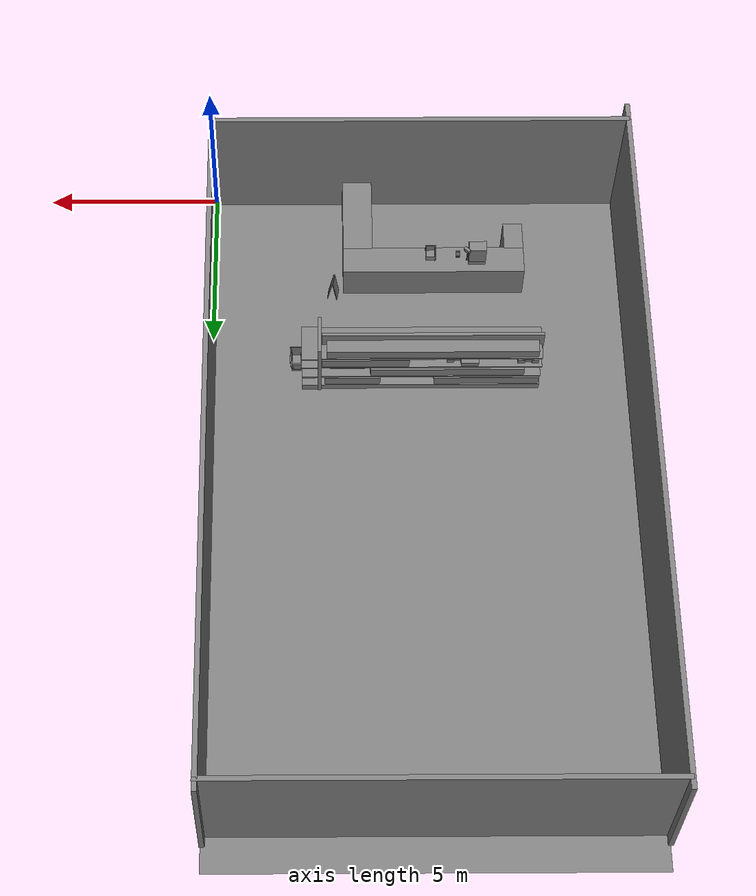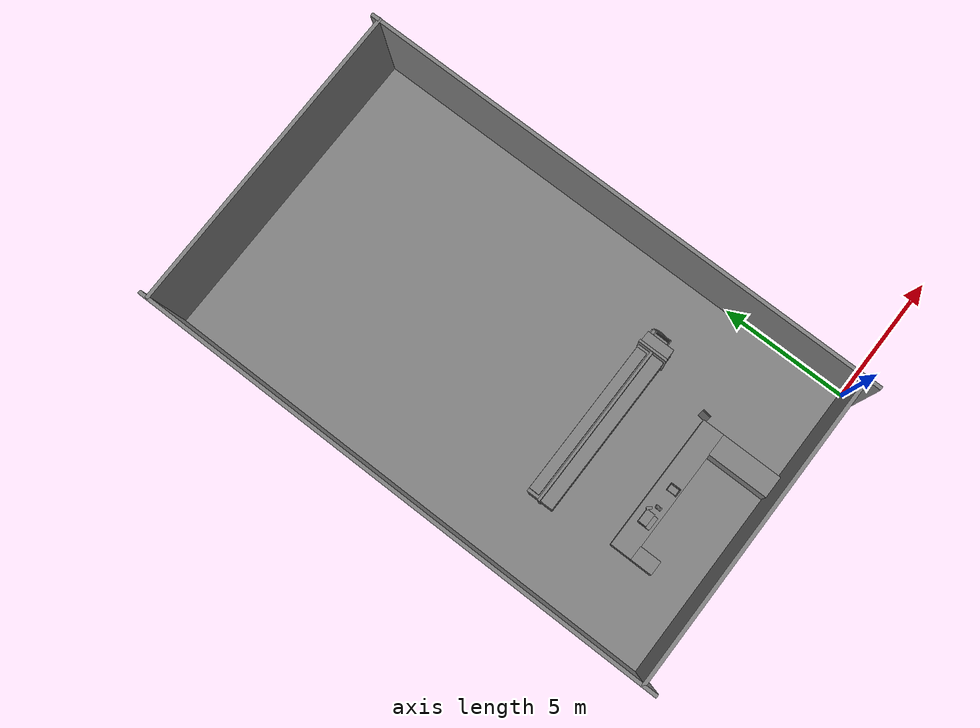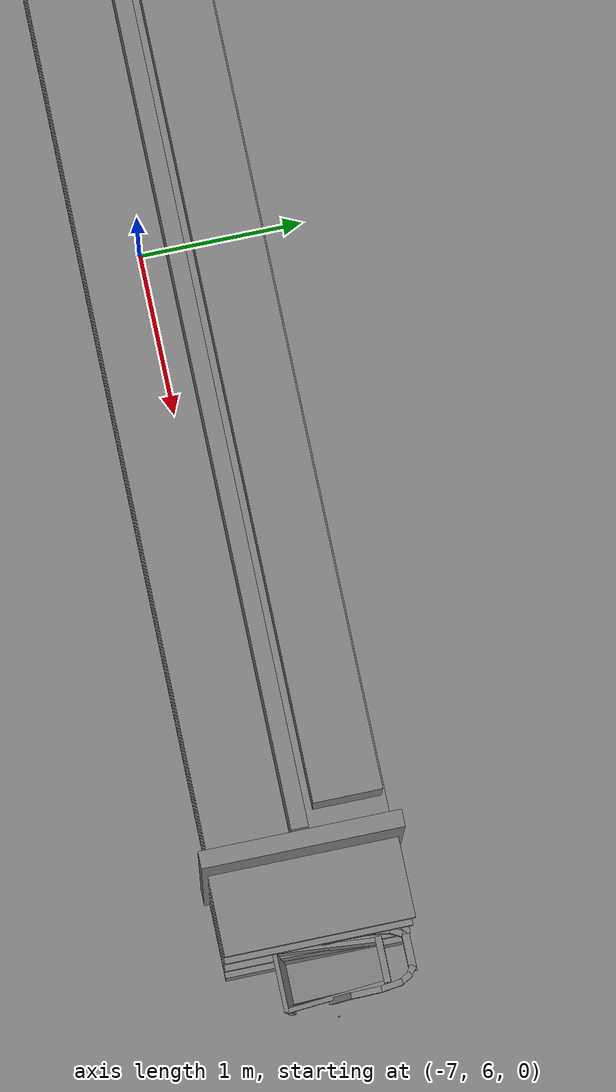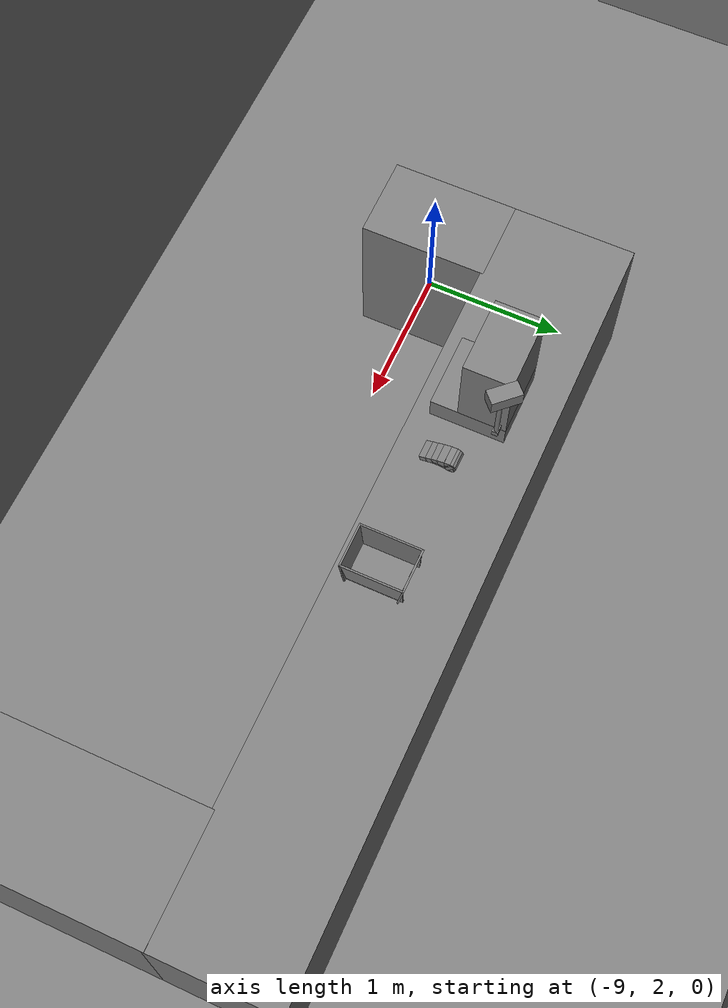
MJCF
<mujoco>
    <option gravity="0.000000000 0.000000000 -9.810000420" timestep="0.0166666" integrator="implicitfast" density="1.225" viscosity="1.8000001e-05" noslip_iterations="10" iterations="100" sdf_iterations="50">
        <flag multiccd="disable"/>
    </option>
    <size memory="1000M"/>
    <compiler coordinate="local"/>
    <worldbody>
        <light cutoff="30" pos="0 1 1" dir="0 -1 -2"/>
        <light cutoff="30" pos="0 -1 1" dir="0 1 -2"/>
        <body pos="-2.436573029 6.404376507 0.137849092" euler="0.000000000 0.000000000 0.000000000" name="[36898982556205]_shoppingtrolley_01">
            <geom contype="1" conaffinity="1" density="1000" type="box" material="" rgba="0.500000000 0.500000000 0.500000000 1.000000000" solimp="0.899999976 0.949999988 0.001000000" friction="1.000000000 0.005000000 0.000100000" solref="0.020000000 1.000000000" margin="0" condim="3" group="0" pos="0.148195267 -0.199506566 0.782808602" quat="0.998808920 0.017156634 0.026950166 0.036880098" size="0.013499999 0.305999994 0.063000001" name="[36898982556205]_geom_EDD5387F_188B_47C7_9C81_262268DF2BF5"/>
            <geom contype="1" conaffinity="1" density="1000" type="box" material="" rgba="0.500000000 0.500000000 0.500000000 1.000000000" solimp="0.899999976 0.949999988 0.001000000" friction="1.000000000 0.005000000 0.000100000" solref="0.020000000 1.000000000" margin="0" condim="3" group="0" pos="-0.000005364 0.100332208 0.734785020" quat="0.999668717 0.025737956 -0.000000010 0.000000000" size="0.135000005 0.019800000 0.152999997" name="[36898982556205]_geom_AF936879_698C_411B_A16E_8BE2845CE928"/>
            <geom contype="1" conaffinity="1" density="1000" type="box" material="" rgba="0.500000000 0.500000000 0.500000000 1.000000000" solimp="0.899999976 0.949999988 0.001000000" friction="1.000000000 0.005000000 0.000100000" solref="0.020000000 1.000000000" margin="0" condim="3" group="0" pos="-0.169898406 -0.043119621 0.915120542" quat="0.687021017 0.726584017 -0.005590606 -0.006832919" size="0.017999999 0.022499999 0.089999996" name="[36898982556205]_geom_1ABFA5EA_5F3B_4984_B8AF_334D2DC6F599"/>
            <geom contype="1" conaffinity="1" density="1000" type="box" material="" rgba="0.500000000 0.500000000 0.500000000 1.000000000" solimp="0.899999976 0.949999988 0.001000000" friction="1.000000000 0.005000000 0.000100000" solref="0.020000000 1.000000000" margin="0" condim="3" group="0" pos="-0.169898406 -0.178061336 0.864131629" quat="0.916343808 -0.400392294 -0.000000045 0.000000030" size="0.017999999 0.022499999 0.089999996" name="[36898982556205]_geom_30748E29_A370_43E0_8C6C_ABBDA51CAF1D"/>
            <geom contype="1" conaffinity="1" density="1000" type="box" material="" rgba="0.500000000 0.500000000 0.500000000 1.000000000" solimp="0.899999976 0.949999988 0.001000000" friction="1.000000000 0.005000000 0.000100000" solref="0.020000000 1.000000000" margin="0" condim="3" group="0" pos="0.103667587 0.233050480 0.912927270" quat="0.634205043 -0.622199059 -0.324503720 0.324576139" size="0.017999999 0.022499999 0.035999998" name="[36898982556205]_geom_D9064F51_C6D0_4343_9106_908B309BC84A"/>
            <geom contype="1" conaffinity="1" density="1000" type="box" material="" rgba="0.500000000 0.500000000 0.500000000 1.000000000" solimp="0.899999976 0.949999988 0.001000000" friction="1.000000000 0.005000000 0.000100000" solref="0.020000000 1.000000000" margin="0" condim="3" group="0" pos="0.169898629 -0.178061336 0.864131629" quat="0.916343808 -0.400392294 -0.000000045 0.000000030" size="0.017999999 0.022499999 0.089999996" name="[36898982556205]_geom_2107BB30_910D_44A8_A969_99F384E32A55"/>
            <geom contype="1" conaffinity="1" density="1000" type="box" material="" rgba="0.500000000 0.500000000 0.500000000 1.000000000" solimp="0.899999976 0.949999988 0.001000000" friction="1.000000000 0.005000000 0.000100000" solref="0.020000000 1.000000000" margin="0" condim="3" group="0" pos="0.169898629 -0.043119621 0.915120542" quat="0.687029123 -0.726576388 -0.006509603 0.005963952" size="0.017999999 0.022499999 0.089999996" name="[36898982556205]_geom_908DF917_7320_4CE0_8FDD_2A33049C5DD9"/>
            <geom contype="1" conaffinity="1" density="1000" type="box" material="" rgba="0.500000000 0.500000000 0.500000000 1.000000000" solimp="0.899999976 0.949999988 0.001000000" friction="1.000000000 0.005000000 0.000100000" solref="0.020000000 1.000000000" margin="0" condim="3" group="0" pos="-0.005004787 0.248085022 0.912686050" quat="1.000000000 0.000000000 0.000000000 0.000000000" size="0.107999995 0.022499999 0.022499999" name="[36898982556205]_geom_63481084_2B67_4CD6_9339_C66DD43D3F70"/>
            <geom contype="1" conaffinity="1" density="1000" type="box" material="" rgba="0.500000000 0.500000000 0.500000000 1.000000000" solimp="0.899999976 0.949999988 0.001000000" friction="1.000000000 0.005000000 0.000100000" solref="0.020000000 1.000000000" margin="0" condim="3" group="0" pos="-0.000004721 -0.174527690 0.560063601" quat="0.996704638 0.081116498 -0.000000004 0.000000000" size="0.126000002 0.287999988 0.009000000" name="[36898982556205]_geom_F697640D_6331_49C5_AB16_72D1A65B6C3E"/>
            <geom contype="1" conaffinity="1" density="1000" type="box" material="" rgba="0.500000000 0.500000000 0.500000000 1.000000000" solimp="0.899999976 0.949999988 0.001000000" friction="1.000000000 0.005000000 0.000100000" solref="0.020000000 1.000000000" margin="0" condim="3" group="0" pos="0.134013891 0.200098798 0.912192523" quat="0.692574680 -0.680924535 -0.166899428 0.169783980" size="0.017999999 0.022499999 0.035999998" name="[36898982556205]_geom_B93BCAF1_F764_4651_87D7_FE7C5B3ABB7B"/>
            <geom contype="1" conaffinity="1" density="1000" type="box" material="" rgba="0.500000000 0.500000000 0.500000000 1.000000000" solimp="0.899999976 0.949999988 0.001000000" friction="1.000000000 0.005000000 0.000100000" solref="0.020000000 1.000000000" margin="0" condim="3" group="0" pos="-0.135714188 -0.191051379 0.694841146" quat="0.997147322 0.056064609 -0.045779683 -0.021407485" size="0.013499999 0.287999988 0.053999998" name="[36898982556205]_geom_07E6C2AC_64A9_4AD3_BE83_8A74246FAC44"/>
            <geom contype="1" conaffinity="1" density="1000" type="box" material="" rgba="0.500000000 0.500000000 0.500000000 1.000000000" solimp="0.899999976 0.949999988 0.001000000" friction="1.000000000 0.005000000 0.000100000" solref="0.020000000 1.000000000" margin="0" condim="3" group="0" pos="0.141839072 -0.191051379 0.702451229" quat="0.997147262 0.056065105 0.045779929 0.021407485" size="0.013499999 0.287999988 0.053999998" name="[36898982556205]_geom_76D9882B_64C3_412D_ACAF_09910251C4F2"/>
            <geom contype="1" conaffinity="1" density="1000" type="box" material="" rgba="0.500000000 0.500000000 0.500000000 1.000000000" solimp="0.899999976 0.949999988 0.001000000" friction="1.000000000 0.005000000 0.000100000" solref="0.020000000 1.000000000" margin="0" condim="3" group="0" pos="-0.142927840 -0.199506134 0.784674108" quat="0.998421252 0.016904408 -0.027109101 -0.046199299" size="0.013499999 0.305999994 0.063000001" name="[36898982556205]_geom_6F58F6C0_2FED_4E12_B56C_C51CBC347576"/>
            <geom contype="1" conaffinity="1" density="1000" type="box" material="" rgba="0.500000000 0.500000000 0.500000000 1.000000000" solimp="0.899999976 0.949999988 0.001000000" friction="1.000000000 0.005000000 0.000100000" solref="0.020000000 1.000000000" margin="0" condim="3" group="0" pos="-0.000006008 -0.484932661 0.670727849" quat="0.997585475 0.069449045 -0.000000004 -0.000000089" size="0.179999992 0.013499999 0.170999989" name="[36898982556205]_geom_7679F7EC_3B43_4533_A215_895E8238E3D9"/>
            <geom contype="1" conaffinity="1" density="1000" type="box" material="" rgba="0.500000000 0.500000000 0.500000000 1.000000000" solimp="0.899999976 0.949999988 0.001000000" friction="1.000000000 0.005000000 0.000100000" solref="0.020000000 1.000000000" margin="0" condim="3" group="0" pos="-0.160832763 0.103427693 0.910528183" quat="0.711469591 0.699786782 -0.048386075 -0.042050660" size="0.017999999 0.022499999 0.071999997" name="[36898982556205]_geom_65702ECB_BCCF_4DAA_919B_4D34F6A4EE3C"/>
            <geom contype="1" conaffinity="1" density="1000" type="box" material="" rgba="0.500000000 0.500000000 0.500000000 1.000000000" solimp="0.899999976 0.949999988 0.001000000" friction="1.000000000 0.005000000 0.000100000" solref="0.020000000 1.000000000" margin="0" condim="3" group="0" pos="0.131482959 -0.182533979 0.598989725" quat="0.996607125 0.055331629 0.059003670 0.015205893" size="0.013499999 0.287999988 0.053999998" name="[36898982556205]_geom_D5165A4F_38BF_4663_A022_0447F10A26DA"/>
            <geom contype="1" conaffinity="1" density="1000" type="box" material="" rgba="0.500000000 0.500000000 0.500000000 1.000000000" solimp="0.899999976 0.949999988 0.001000000" friction="1.000000000 0.005000000 0.000100000" solref="0.020000000 1.000000000" margin="0" condim="3" group="0" pos="-0.134013891 0.200098798 0.912192523" quat="0.694057047 0.679413557 -0.172947660 -0.163618833" size="0.017999999 0.022499999 0.035999998" name="[36898982556205]_geom_024A3829_2759_42A2_8593_20A9812F9F1A"/>
            <geom contype="1" conaffinity="1" density="1000" type="box" material="" rgba="0.500000000 0.500000000 0.500000000 1.000000000" solimp="0.899999976 0.949999988 0.001000000" friction="1.000000000 0.005000000 0.000100000" solref="0.020000000 1.000000000" margin="0" condim="3" group="0" pos="-0.126757339 -0.182533979 0.598989725" quat="0.996607184 0.055331606 -0.059003651 -0.015205891" size="0.013499999 0.287999988 0.053999998" name="[36898982556205]_geom_9BC34D6F_DA7B_49E3_B080_976138704E7E"/>
            <geom contype="1" conaffinity="1" density="1000" type="box" material="" rgba="0.500000000 0.500000000 0.500000000 1.000000000" solimp="0.899999976 0.949999988 0.001000000" friction="1.000000000 0.005000000 0.000100000" solref="0.020000000 1.000000000" margin="0" condim="3" group="0" pos="-0.107458733 0.238907143 0.911498845" quat="0.634576976 0.622505128 -0.330067992 -0.317575932" size="0.017999999 0.022499999 0.035999998" name="[36898982556205]_geom_906471A8_4968_4317_9351_E8E720130727"/>
            <geom contype="1" conaffinity="1" density="1000" type="box" material="" rgba="0.500000000 0.500000000 0.500000000 1.000000000" solimp="0.899999976 0.949999988 0.001000000" friction="1.000000000 0.005000000 0.000100000" solref="0.020000000 1.000000000" margin="0" condim="3" group="0" pos="0.160832971 0.103427693 0.910528183" quat="0.711112797 -0.700149298 -0.042821646 0.047705106" size="0.017999999 0.022499999 0.071999997" name="[36898982556205]_geom_31AF40AF_D86E_414D_A360_A25DAE2E8DC3"/>
            <site size="0.005000000 0.005000000 0.005000000" rgba="0.500000000 0.500000000 0.500000000 1.000000000" pos="0.000000000 0.000000000 0.000000000" quat="1.000000000 0.000000000 0.000000000 0.000000000" group="0" type="sphere" name="[36898982556205]_shoppingtrolley_01"/>
        </body>
        <body pos="-7.168000221 2.823999882 1.227496982" euler="-0.283413887 0.056829713 -0.133293241" name="openloong_gripper_2f85_fix_base_usda_Pos">
            <geom contype="1" conaffinity="1" density="1000" type="box" material="" rgba="0.500000000 0.500000000 0.500000000 1.000000000" solimp="0.899999976 0.949999988 0.001000000" friction="1.000000000 0.005000000 0.000100000" solref="0.020000000 1.000000000" margin="0" condim="3" group="0" pos="-0.002278805 0.074524641 -0.004134178" quat="0.315989256 0.948762834 0.000000000 0.000000000" size="0.059999999 0.013000000 0.035000000" name="openloong_gripper_2f85_fix_base_usda_geom_6FDDB44B_6C59_4EEA_864C_CBA0C56FCAA6"/>
            <geom contype="1" conaffinity="1" density="1000" type="box" material="" rgba="0.500000000 0.500000000 0.500000000 1.000000000" solimp="0.899999976 0.949999988 0.001000000" friction="1.000000000 0.005000000 0.000100000" solref="0.020000000 1.000000000" margin="0" condim="3" group="0" pos="-0.002278805 0.078031301 0.008128285" quat="0.990447283 -0.137893349 -0.000000000 0.000000000" size="0.059999999 0.010000000 0.035000000" name="openloong_gripper_2f85_fix_base_usda_geom_E3F333E5_8F13_4418_918D_9169E0BC0DE2"/>
            <geom contype="1" conaffinity="1" density="1000" type="box" material="" rgba="0.500000000 0.500000000 0.500000000 1.000000000" solimp="0.899999976 0.949999988 0.001000000" friction="1.000000000 0.005000000 0.000100000" solref="0.020000000 1.000000000" margin="0" condim="3" group="0" pos="-0.002278805 0.080785275 -0.002596974" quat="0.287325412 -0.957833171 0.000000000 -0.000000000" size="0.059999999 0.013000000 0.035000000" name="openloong_gripper_2f85_fix_base_usda_geom_F36FA871_0849_4F55_87A0_3CCF3F53EE5D"/>
            <geom contype="1" conaffinity="1" density="1000" type="box" material="" rgba="0.500000000 0.500000000 0.500000000 1.000000000" solimp="0.899999976 0.949999988 0.001000000" friction="1.000000000 0.005000000 0.000100000" solref="0.020000000 1.000000000" margin="0" condim="3" group="0" pos="-0.002278805 -0.098804474 -0.020147085" quat="0.988851428 0.148906425 0.000000000 -0.000000000" size="0.059999999 0.022000000 0.020000000" name="openloong_gripper_2f85_fix_base_usda_geom_22A42F31_CC4A_4A69_9781_3AB60241A954"/>
            <geom contype="1" conaffinity="1" density="1000" type="box" material="" rgba="0.500000000 0.500000000 0.500000000 1.000000000" solimp="0.899999976 0.949999988 0.001000000" friction="1.000000000 0.005000000 0.000100000" solref="0.020000000 1.000000000" margin="0" condim="3" group="0" pos="-0.002279282 0.019920349 0.012102842" quat="0.995421529 0.095583312 -0.000000000 0.000000000" size="0.059999999 0.025000000 0.026000001" name="openloong_gripper_2f85_fix_base_usda_geom_705514F1_EF7C_4F4D_AEA7_F1B999D8593C"/>
            <geom contype="1" conaffinity="1" density="1000" type="box" material="" rgba="0.500000000 0.500000000 0.500000000 1.000000000" solimp="0.899999976 0.949999988 0.001000000" friction="1.000000000 0.005000000 0.000100000" solref="0.020000000 1.000000000" margin="0" condim="3" group="0" pos="-0.002279282 0.005734444 -0.014276981" quat="0.999571502 -0.029275293 -0.000000000 0.000000000" size="0.059999999 0.050000001 0.010000000" name="openloong_gripper_2f85_fix_base_usda_geom_A95F7EF9_9068_4C96_991F_AAE120A9B010"/>
            <geom contype="1" conaffinity="1" density="1000" type="box" material="" rgba="0.500000000 0.500000000 0.500000000 1.000000000" solimp="0.899999976 0.949999988 0.001000000" friction="1.000000000 0.005000000 0.000100000" solref="0.020000000 1.000000000" margin="0" condim="3" group="0" pos="-0.002278805 0.079460382 0.007771969" quat="0.922590315 -0.385781497 -0.000000000 0.000000000" size="0.059999999 0.010000000 0.035000000" name="openloong_gripper_2f85_fix_base_usda_geom_E3E36E00_0258_4393_8103_3BF037E4975B"/>
            <geom contype="1" conaffinity="1" density="1000" type="box" material="" rgba="0.500000000 0.500000000 0.500000000 1.000000000" solimp="0.899999976 0.949999988 0.001000000" friction="1.000000000 0.005000000 0.000100000" solref="0.020000000 1.000000000" margin="0" condim="3" group="0" pos="-0.002279282 0.081384182 -0.001320124" quat="0.590483606 -0.807049692 0.000000000 0.000000000" size="0.059999999 0.013000000 0.035000000" name="openloong_gripper_2f85_fix_base_usda_geom_82FB0F94_0D4A_4052_87FA_3AED22A742C4"/>
            <geom contype="1" conaffinity="1" density="1000" type="box" material="" rgba="0.500000000 0.500000000 0.500000000 1.000000000" solimp="0.899999976 0.949999988 0.001000000" friction="1.000000000 0.005000000 0.000100000" solref="0.020000000 1.000000000" margin="0" condim="3" group="0" pos="-0.002278805 -0.059297562 -0.007972836" quat="0.988851428 0.148906425 0.000000000 -0.000000000" size="0.059999999 0.020000000 0.022000000" name="openloong_gripper_2f85_fix_base_usda_geom_58D7F62E_1FAD_4D72_96C8_2FF44857BB36"/>
            <geom contype="1" conaffinity="1" density="1000" type="box" material="" rgba="0.500000000 0.500000000 0.500000000 1.000000000" solimp="0.899999976 0.949999988 0.001000000" friction="1.000000000 0.005000000 0.000100000" solref="0.020000000 1.000000000" margin="0" condim="3" group="0" pos="-0.002278805 0.076618671 -0.004656911" quat="0.004634960 0.999989390 -0.000000000 0.000000000" size="0.059999999 0.013000000 0.035000000" name="openloong_gripper_2f85_fix_base_usda_geom_85556365_FA46_46E1_B2F4_7390054CE883"/>
            <geom contype="1" conaffinity="1" density="1000" type="box" material="" rgba="0.500000000 0.500000000 0.500000000 1.000000000" solimp="0.899999976 0.949999988 0.001000000" friction="1.000000000 0.005000000 0.000100000" solref="0.020000000 1.000000000" margin="0" condim="3" group="0" pos="-0.002279282 -0.021952629 0.002959967" quat="0.991270185 0.131847635 0.000000000 -0.000000000" size="0.059999999 0.020000000 0.024000000" name="openloong_gripper_2f85_fix_base_usda_geom_909DE2A1_566F_405B_9844_5299AF6CBF6C"/>
            <geom contype="1" conaffinity="1" density="1000" type="box" material="" rgba="0.500000000 0.500000000 0.500000000 1.000000000" solimp="0.899999976 0.949999988 0.001000000" friction="1.000000000 0.005000000 0.000100000" solref="0.020000000 1.000000000" margin="0" condim="3" group="0" pos="-0.002278805 0.081418991 0.002587795" quat="0.803492188 -0.595315576 0.000000000 0.000000000" size="0.059999999 0.013000000 0.035000000" name="openloong_gripper_2f85_fix_base_usda_geom_85EF2B1F_21AE_4D83_A60D_53411B87A1A3"/>
            <geom contype="1" conaffinity="1" density="1000" type="box" material="" rgba="0.500000000 0.500000000 0.500000000 1.000000000" solimp="0.899999976 0.949999988 0.001000000" friction="1.000000000 0.005000000 0.000100000" solref="0.020000000 1.000000000" margin="0" condim="3" group="0" pos="-0.002278805 0.061115503 0.008545756" quat="0.999325931 0.036714435 -0.000000000 -0.000000000" size="0.059999999 0.020000000 0.035000000" name="openloong_gripper_2f85_fix_base_usda_geom_D82D4264_5C8E_4CBA_930B_6C37D283D3F3"/>
            <freejoint name="openloong_gripper_2f85_fix_base_usda_pos_scan"/>
        </body>
        <body pos="-6.332345009 2.779978037 1.034067392" euler="0.000000000 0.000000000 0.000000000" name="openloong_gripper_2f85_fix_base_usda_basket">
            <geom contype="1" conaffinity="1" density="100000" type="box" material="" rgba="0.500000000 0.500000000 0.500000000 1.000000000" solimp="0.899999976 0.949999988 0.001000000" friction="1.000000000 0.899999976 0.000100000" solref="0.020000000 1.000000000" margin="0" condim="3" group="0" pos="-0.172339439 0.000000000 0.168361664" quat="0.706172407 -0.036353018 -0.036353093 0.706170976" size="0.200000003 0.006000000 0.108000003" name="openloong_gripper_2f85_fix_base_usda_geom_BE08C045_6746_47EC_AA7F_19D50321ADD5"/>
            <geom contype="1" conaffinity="1" density="100000" type="box" material="" rgba="0.500000000 0.500000000 0.500000000 1.000000000" solimp="0.899999976 0.949999988 0.001000000" friction="1.000000000 0.899999976 0.000100000" solref="0.020000000 1.000000000" margin="0" condim="3" group="0" pos="-0.039724827 -0.188568115 0.167089701" quat="0.997537494 0.070135131 0.000000000 0.000000000" size="0.150000006 0.006000000 0.108000003" name="openloong_gripper_2f85_fix_base_usda_geom_5BD234F2_4FBA_4A70_A87E_78A34EACA28D"/>
            <geom contype="1" conaffinity="1" density="100000" type="box" material="" rgba="0.500000000 0.500000000 0.500000000 1.000000000" solimp="0.899999976 0.949999988 0.001000000" friction="1.000000000 0.899999976 0.000100000" solref="0.020000000 1.000000000" margin="0" condim="3" group="0" pos="-0.039724827 0.188377380 0.167089701" quat="0.997489929 -0.070808925 0.000000000 0.000000000" size="0.150000006 0.006000000 0.108000003" name="openloong_gripper_2f85_fix_base_usda_geom_00918233_D360_4E96_A859_CB998063E7F3"/>
            <geom contype="1" conaffinity="1" density="100000" type="box" material="" rgba="0.500000000 0.500000000 0.500000000 1.000000000" solimp="0.899999976 0.949999988 0.001000000" friction="1.000000000 0.899999976 0.000100000" solref="0.020000000 1.000000000" margin="0" condim="3" group="0" pos="-0.039724827 0.000000000 0.068126202" quat="1.000000000 0.000000000 0.000000000 0.000000000" size="0.129999995 0.174999997 0.006000000" name="openloong_gripper_2f85_fix_base_usda_geom_F40EBFEE_9D56_4F71_835A_B558FE234942"/>
            <geom contype="1" conaffinity="1" density="100000" type="box" material="" rgba="0.500000000 0.500000000 0.500000000 1.000000000" solimp="0.899999976 0.949999988 0.001000000" friction="1.000000000 0.899999976 0.000100000" solref="0.020000000 1.000000000" margin="0" condim="3" group="0" pos="0.094372749 0.000000000 0.168361664" quat="0.706172049 0.036353335 0.036353379 0.706171215" size="0.200000003 0.006000000 0.108000003" name="openloong_gripper_2f85_fix_base_usda_geom_26AFC22D_35AC_49D7_AAA0_5373B125BE0F"/>
            <freejoint name="openloong_gripper_2f85_fix_base_usda_basket_joint"/>
            <site size="0.005000000 0.005000000 0.005000000" rgba="0.500000000 0.500000000 0.500000000 1.000000000" pos="0.000000000 0.000000000 0.000000000" quat="1.000000000 0.000000000 0.000000000 0.000000000" group="0" type="sphere" name="openloong_gripper_2f85_fix_base_usda_basketsite"/>
        </body>
        <body pos="-3.510578632 3.403555870 -0.000000100" euler="0.000000000 0.000000000 40.200675964" name="openloong_gripper_2f85_fix_base_usda_PZ">
            <geom contype="1" conaffinity="1" density="1000" type="box" material="" rgba="0.500000000 0.500000000 0.500000000 1.000000000" solimp="0.899999976 0.949999988 0.001000000" friction="1.000000000 0.005000000 0.000100000" solref="0.020000000 1.000000000" margin="0" condim="3" group="0" pos="-0.047453165 0.056484699 0.373715430" quat="0.934750080 0.077914521 0.028795123 0.345459938" size="0.180000007 0.010000000 0.379999995" name="openloong_gripper_2f85_fix_base_usda_geom_7575CCA4_0E4B_49B6_88C3_D7ED312FD056"/>
            <geom contype="1" conaffinity="1" density="1000" type="box" material="" rgba="0.500000000 0.500000000 0.500000000 1.000000000" solimp="0.899999976 0.949999988 0.001000000" friction="1.000000000 0.005000000 0.000100000" solref="0.020000000 1.000000000" margin="0" condim="3" group="0" pos="0.047452450 -0.054376602 0.374072611" quat="0.934387863 -0.082143910 -0.030358355 0.345326364" size="0.180000007 0.010000000 0.379999995" name="openloong_gripper_2f85_fix_base_usda_geom_E92D890C_7216_4FD2_8A0E_B5507B20E510"/>
            <freejoint name="openloong_gripper_2f85_fix_base_usda_PZ"/>
        </body>
        <body pos="0.000000000 0.000000000 0.000000000" euler="0.000000000 0.000000000 0.000000000" name="Interactive Objects_Interactive Objects"/>
        <body pos="0.000000000 0.000000000 0.000000000" euler="0.000000000 0.000000000 0.000000000" name=" Static Objects_ Static Objects">
            <geom contype="1" conaffinity="1" density="1000" type="box" material="" rgba="0.500000000 0.500000000 0.500000000 1.000000000" solimp="0.899999976 0.949999988 0.001000000" friction="1.000000000 0.005000000 0.000100000" solref="0.020000000 1.000000000" margin="0" condim="3" group="0" pos="-3.101639986 6.150595188 1.018643856" quat="1.000000000 0.000000000 0.000000000 0.000000000" size="0.050000001 0.579999983 1.019999981" name=" Static Objects_geom_63940E00_9D68_4BB2_AABE_2DA397B9F022"/>
            <geom contype="1" conaffinity="1" density="1000" type="box" material="" rgba="0.500000000 0.500000000 0.500000000 1.000000000" solimp="0.899999976 0.949999988 0.001000000" friction="1.000000000 0.005000000 0.000100000" solref="0.020000000 1.000000000" margin="0" condim="3" group="0" pos="-2.825197220 6.153595448 1.115278244" quat="0.707107067 0.000000000 0.000000000 0.707106471" size="0.550000012 0.239999995 0.025000000" name=" Static Objects_geom_0806A041_5965_40BE_B364_D9BEE934185D"/>
            <geom contype="1" conaffinity="1" density="1000" type="box" material="" rgba="0.500000000 0.500000000 0.500000000 1.000000000" solimp="0.899999976 0.949999988 0.001000000" friction="1.000000000 0.005000000 0.000100000" solref="0.020000000 1.000000000" margin="0" condim="3" group="0" pos="-2.825197220 6.153595448 0.097434282" quat="0.707107067 0.000000000 0.000000000 0.707106471" size="0.550000012 0.239999995 0.098999999" name=" Static Objects_geom_812ED207_DECE_47D1_9152_B194DDE809A3"/>
            <geom contype="1" conaffinity="1" density="1000" type="box" material="" rgba="0.500000000 0.500000000 0.500000000 1.000000000" solimp="0.899999976 0.949999988 0.001000000" friction="1.000000000 0.005000000 0.000100000" solref="0.020000000 1.000000000" margin="0" condim="3" group="0" pos="-6.293097973 6.153595448 1.114443064" quat="0.707107067 0.000000000 0.000000000 0.707106471" size="0.529999971 3.134999990 0.025000000" name=" Static Objects_geom_96D2B94A_BC1F_45FB_81FE_AAC09C35856A"/>
            <geom contype="1" conaffinity="1" density="1000" type="box" material="" rgba="0.500000000 0.500000000 0.500000000 1.000000000" solimp="0.899999976 0.949999988 0.001000000" friction="1.000000000 0.005000000 0.000100000" solref="0.020000000 1.000000000" margin="0" condim="3" group="0" pos="-2.825197220 6.153595448 1.563861728" quat="0.707107067 0.000000000 0.000000000 0.707106471" size="0.550000012 0.239999995 0.025000000" name=" Static Objects_geom_642094AA_73C7_435D_B029_4D0142A88C55"/>
            <geom contype="1" conaffinity="1" density="1000" type="box" material="" rgba="0.500000000 0.500000000 0.500000000 1.000000000" solimp="0.899999976 0.949999988 0.001000000" friction="1.000000000 0.005000000 0.000100000" solref="0.020000000 1.000000000" margin="0" condim="3" group="0" pos="-6.311686516 6.153595448 1.018643856" quat="0.707107067 0.000000000 0.000000000 0.707106471" size="0.050000001 3.150000095 1.019999981" name=" Static Objects_geom_7E74522C_8947_4624_8CF3_E407ADE78824"/>
            <geom contype="1" conaffinity="1" density="1000" type="box" material="" rgba="0.500000000 0.500000000 0.500000000 1.000000000" solimp="0.899999976 0.949999988 0.001000000" friction="1.000000000 0.005000000 0.000100000" solref="0.020000000 1.000000000" margin="0" condim="3" group="0" pos="-6.286010742 6.153595448 0.096129179" quat="0.707107067 0.000000000 0.000000000 0.707106471" size="0.529999971 3.134999990 0.098999999" name=" Static Objects_geom_9FEC7363_18F1_4746_B19F_61DC3EE1972D"/>
            <geom contype="1" conaffinity="1" density="1000" type="box" material="" rgba="0.500000000 0.500000000 0.500000000 1.000000000" solimp="0.899999976 0.949999988 0.001000000" friction="1.000000000 0.005000000 0.000100000" solref="0.020000000 1.000000000" margin="0" condim="3" group="0" pos="-2.825197220 6.153595448 0.629031777" quat="0.707107067 0.000000000 0.000000000 0.707106471" size="0.550000012 0.239999995 0.025000000" name=" Static Objects_geom_6341DD1F_105F_485F_A7AF_ABA04B14578A"/>
            <geom contype="1" conaffinity="1" density="1000" type="box" material="" rgba="0.500000000 0.500000000 0.500000000 1.000000000" solimp="0.899999976 0.949999988 0.001000000" friction="1.000000000 0.005000000 0.000100000" solref="0.020000000 1.000000000" margin="0" condim="3" group="0" pos="-6.286010742 6.153595448 1.563861728" quat="0.707107067 0.000000000 0.000000000 0.707106471" size="0.529999971 3.134999990 0.025000000" name=" Static Objects_geom_E3151CD0_DA04_427F_9511_8D856C93BEC9"/>
            <geom contype="1" conaffinity="1" density="1000" type="box" material="" rgba="0.500000000 0.500000000 0.500000000 1.000000000" solimp="0.899999976 0.949999988 0.001000000" friction="1.000000000 0.005000000 0.000100000" solref="0.020000000 1.000000000" margin="0" condim="3" group="0" pos="-6.286010742 6.153595448 0.629031777" quat="0.707107067 0.000000000 0.000000000 0.707106471" size="0.529999971 3.134999990 0.025000000" name=" Static Objects_geom_F1394EF5_5AFE_4DA4_BD7B_C9264F378B77"/>
            <geom contype="1" conaffinity="1" density="1000" type="box" material="" rgba="0.500000000 0.500000000 0.500000000 1.000000000" solimp="0.899999976 0.949999988 0.001000000" friction="1.000000000 0.005000000 0.000100000" solref="0.020000000 1.000000000" margin="0" condim="3" group="0" pos="-7.719123363 2.867671013 1.173410416" quat="1.000000000 0.000000000 0.000000000 0.000000000" size="0.250000000 0.250000000 0.079999998" name=" Static Objects_geom_50559442_86B1_421E_B932_E6CC5DE7CA88"/>
            <geom contype="1" conaffinity="1" density="1000" type="box" material="" rgba="0.500000000 0.500000000 0.500000000 1.000000000" solimp="0.899999976 0.949999988 0.001000000" friction="1.000000000 0.005000000 0.000100000" solref="0.020000000 1.000000000" margin="0" condim="3" group="0" pos="-7.408766270 3.088089943 1.776644945" quat="0.928051054 0.000000000 0.000000000 0.372453064" size="0.050000001 0.100000001 0.050000001" name=" Static Objects_geom_DD9ECAB8_0C43_4293_B2F8_40D4551C88DF"/>
            <geom contype="1" conaffinity="1" density="1000" type="box" material="" rgba="0.500000000 0.500000000 0.500000000 1.000000000" solimp="0.899999976 0.949999988 0.001000000" friction="1.000000000 0.005000000 0.000100000" solref="0.020000000 1.000000000" margin="0" condim="3" group="0" pos="-7.719123363 2.958004713 1.530241251" quat="1.000000000 0.000000000 0.000000000 0.000000000" size="0.250000000 0.159999996 0.280000001" name=" Static Objects_geom_1385CBF1_0670_4ED1_8C71_72A61A7CACF2"/>
            <geom contype="1" conaffinity="1" density="1000" type="cylinder" material="" rgba="0.500000000 0.500000000 0.500000000 1.000000000" solimp="0.899999976 0.949999988 0.001000000" friction="1.000000000 0.005000000 0.000100000" solref="0.020000000 1.000000000" margin="0" condim="3" group="0" pos="-7.427312374 3.069516420 1.502544641" quat="0.928051054 0.000000000 0.000000000 0.372453064" size="0.015000000 0.230000004 0.100000001" name=" Static Objects_geom_F4B7AA1F_177A_4DEA_A911_99CA57C01D6E"/>
            <geom contype="1" conaffinity="1" density="1000" type="box" material="" rgba="0.500000000 0.500000000 0.500000000 1.000000000" solimp="0.899999976 0.949999988 0.001000000" friction="1.000000000 0.005000000 0.000100000" solref="0.020000000 1.000000000" margin="0" condim="3" group="0" pos="-7.437745571 3.067511320 1.289965630" quat="1.000000000 0.000000000 0.000000000 0.000000000" size="0.029999999 0.020000000 0.020000000" name=" Static Objects_geom_B23E5328_9511_469A_BFA1_8F4730CC17AC"/>
            <geom contype="1" conaffinity="1" density="1000" type="box" material="" rgba="0.500000000 0.500000000 0.500000000 1.000000000" solimp="0.899999976 0.949999988 0.001000000" friction="1.000000000 0.005000000 0.000100000" solref="0.020000000 1.000000000" margin="0" condim="3" group="0" pos="-9.058088303 6.434794426 1.209077358" quat="1.000000000 0.000000000 0.000000000 0.000000000" size="0.250000000 0.100000001 0.070000000" name=" Static Objects_geom_1F303A08_C5B1_495C_AE80_67E372714F88"/>
            <geom contype="1" conaffinity="1" density="1000" type="box" material="" rgba="0.500000000 0.500000000 0.500000000 1.000000000" solimp="0.899999976 0.949999988 0.001000000" friction="1.000000000 0.005000000 0.000100000" solref="0.020000000 1.000000000" margin="0" condim="3" group="0" pos="-7.886891365 6.459744930 0.352518857" quat="1.000000000 0.000000000 0.000000000 0.000000000" size="1.500000000 0.200000003 0.150000006" name=" Static Objects_geom_B0696E82_4F81_44DC_B146_A42CA22F70A6"/>
            <geom contype="1" conaffinity="1" density="1000" type="box" material="" rgba="0.500000000 0.500000000 0.500000000 1.000000000" solimp="0.899999976 0.949999988 0.001000000" friction="1.000000000 0.005000000 0.000100000" solref="0.020000000 1.000000000" margin="0" condim="3" group="0" pos="-9.237723351 6.464855671 1.209077358" quat="1.000000000 0.000000000 0.000000000 0.000000000" size="0.100000001 0.100000001 0.070000000" name=" Static Objects_geom_5E67190D_94C7_4E09_AA44_F7D9C8D164CC"/>
            <geom contype="1" conaffinity="1" density="1000" type="box" material="" rgba="0.500000000 0.500000000 0.500000000 1.000000000" solimp="0.899999976 0.949999988 0.001000000" friction="1.000000000 0.005000000 0.000100000" solref="0.020000000 1.000000000" margin="0" condim="3" group="0" pos="-6.924745083 6.362090111 1.214329123" quat="1.000000000 0.000000000 0.000000000 0.000000000" size="0.200000003 0.100000001 0.075000003" name=" Static Objects_geom_30FC6DCC_34E7_4920_A135_A72412A6170D"/>
            <geom contype="1" conaffinity="1" density="1000" type="box" material="" rgba="0.500000000 0.500000000 0.500000000 1.000000000" solimp="0.899999976 0.949999988 0.001000000" friction="1.000000000 0.005000000 0.000100000" solref="0.020000000 1.000000000" margin="0" condim="3" group="0" pos="-4.407354832 6.459744930 1.292199373" quat="1.000000000 0.000000000 0.000000000 0.000000000" size="1.240000010 0.200000003 0.150000006" name=" Static Objects_geom_FECFDAF7_B04B_4979_B457_0E6CA0CC6F4D"/>
            <geom contype="1" conaffinity="1" density="1000" type="box" material="" rgba="0.500000000 0.500000000 0.500000000 1.000000000" solimp="0.899999976 0.949999988 0.001000000" friction="1.000000000 0.005000000 0.000100000" solref="0.020000000 1.000000000" margin="0" condim="3" group="0" pos="-5.611940861 6.318420410 0.350975692" quat="1.000000000 0.000000000 0.000000000 0.000000000" size="0.699999988 0.100000001 0.150000006" name=" Static Objects_geom_ECB313B7_9B9C_42E3_8446_4C705EFB9B7E"/>
            <geom contype="1" conaffinity="1" density="1000" type="box" material="" rgba="0.500000000 0.500000000 0.500000000 1.000000000" solimp="0.899999976 0.949999988 0.001000000" friction="1.000000000 0.005000000 0.000100000" solref="0.020000000 1.000000000" margin="0" condim="3" group="0" pos="-6.300771236 6.459744930 1.744376063" quat="1.000000000 0.000000000 0.000000000 0.000000000" size="3.000000000 0.200000003 0.150000006" name=" Static Objects_geom_09FBFAE0_581D_4FEB_B207_CA7D4E84E04B"/>
            <geom contype="1" conaffinity="1" density="1000" type="box" material="" rgba="0.500000000 0.500000000 0.500000000 1.000000000" solimp="0.899999976 0.949999988 0.001000000" friction="1.000000000 0.005000000 0.000100000" solref="0.020000000 1.000000000" margin="0" condim="3" group="0" pos="-8.844120979 6.464855671 1.209077358" quat="1.000000000 0.000000000 0.000000000 0.000000000" size="0.100000001 0.100000001 0.070000000" name=" Static Objects_geom_1A79F8A7_6542_4D82_8D21_559AB8339F8A"/>
            <geom contype="1" conaffinity="1" density="1000" type="box" material="" rgba="0.500000000 0.500000000 0.500000000 1.000000000" solimp="0.899999976 0.949999988 0.001000000" friction="1.000000000 0.005000000 0.000100000" solref="0.020000000 1.000000000" margin="0" condim="3" group="0" pos="-6.824534416 6.447464466 1.212718010" quat="1.000000000 0.000000000 0.000000000 0.000000000" size="0.100000001 0.100000001 0.075000003" name=" Static Objects_geom_A1F3297A_0E74_4D39_A09F_9AA18AE9CA5B"/>
            <geom contype="1" conaffinity="1" density="1000" type="box" material="" rgba="0.500000000 0.500000000 0.500000000 1.000000000" solimp="0.899999976 0.949999988 0.001000000" friction="1.000000000 0.005000000 0.000100000" solref="0.020000000 1.000000000" margin="0" condim="3" group="0" pos="-6.751636982 6.459744930 0.800981164" quat="1.000000000 0.000000000 0.000000000 0.000000000" size="2.200000048 0.200000003 0.150000006" name=" Static Objects_geom_4546976F_D756_4855_9711_F7132149FBEF"/>
            <geom contype="1" conaffinity="1" density="1000" type="box" material="" rgba="0.500000000 0.500000000 0.500000000 1.000000000" solimp="0.899999976 0.949999988 0.001000000" friction="1.000000000 0.005000000 0.000100000" solref="0.020000000 1.000000000" margin="0" condim="3" group="0" pos="-6.098561764 6.327973843 1.292199373" quat="1.000000000 0.000000000 0.000000000 0.000000000" size="0.500000000 0.100000001 0.150000006" name=" Static Objects_geom_A23FBE60_9845_4E09_92A9_BDA5921F436B"/>
            <geom contype="1" conaffinity="1" density="1000" type="box" material="" rgba="0.500000000 0.500000000 0.500000000 1.000000000" solimp="0.899999976 0.949999988 0.001000000" friction="1.000000000 0.005000000 0.000100000" solref="0.020000000 1.000000000" margin="0" condim="3" group="0" pos="-3.907610416 6.318625927 0.800981164" quat="1.000000000 0.000000000 0.000000000 0.000000000" size="0.500000000 0.100000001 0.150000006" name=" Static Objects_geom_1DD17F52_A9EA_4ABF_87EB_179BBDAE3369"/>
            <geom contype="1" conaffinity="1" density="1000" type="box" material="" rgba="0.500000000 0.500000000 0.500000000 1.000000000" solimp="0.899999976 0.949999988 0.001000000" friction="1.000000000 0.005000000 0.000100000" solref="0.020000000 1.000000000" margin="0" condim="3" group="0" pos="-7.373087406 6.458900928 1.214329123" quat="1.000000000 0.000000000 0.000000000 0.000000000" size="0.250000000 0.200000003 0.075000003" name=" Static Objects_geom_658BE301_4F72_4BEC_AA04_3DDF3E21F71A"/>
            <geom contype="1" conaffinity="1" density="1000" type="box" material="" rgba="0.500000000 0.500000000 0.500000000 1.000000000" solimp="0.899999976 0.949999988 0.001000000" friction="1.000000000 0.005000000 0.000100000" solref="0.020000000 1.000000000" margin="0" condim="3" group="0" pos="-4.035642624 6.459744930 0.352518857" quat="1.000000000 0.000000000 0.000000000 0.000000000" size="0.800000012 0.200000003 0.150000006" name=" Static Objects_geom_AC0837CF_CA4B_4E05_B81E_38041808548E"/>
            <geom contype="1" conaffinity="1" density="1000" type="box" material="" rgba="0.500000000 0.500000000 0.500000000 1.000000000" solimp="0.899999976 0.949999988 0.001000000" friction="1.000000000 0.005000000 0.000100000" solref="0.020000000 1.000000000" margin="0" condim="3" group="0" pos="-6.460197449 2.937205315 0.548931718" quat="1.000000000 0.000000000 0.000000000 0.000000000" size="2.650000095 0.430000007 0.550000012" name=" Static Objects_geom_57F433AD_C62D_45DE_B163_204B33939928"/>
            <geom contype="1" conaffinity="1" density="1000" type="box" material="" rgba="0.500000000 0.500000000 0.500000000 1.000000000" solimp="0.899999976 0.949999988 0.001000000" friction="1.000000000 0.005000000 0.000100000" solref="0.020000000 1.000000000" margin="0" condim="3" group="0" pos="-4.240264893 1.327049494 0.549888909" quat="1.000000000 0.000000000 0.000000000 0.000000000" size="0.430000007 1.200000048 0.550000012" name=" Static Objects_geom_4BB26464_45A2_4E99_B253_FBC9F36C8C3B"/>
            <geom contype="1" conaffinity="1" density="1000" type="box" material="" rgba="0.500000000 0.500000000 0.500000000 1.000000000" solimp="0.899999976 0.949999988 0.001000000" friction="1.000000000 0.005000000 0.000100000" solref="0.020000000 1.000000000" margin="0" condim="3" group="0" pos="-8.830721855 2.096410990 0.549305558" quat="1.000000000 0.000000000 0.000000000 0.000000000" size="0.280000001 0.430000007 0.550000012" name=" Static Objects_geom_EDA88FD1_898F_48F5_A889_898AB20241A4"/>
            <geom contype="1" conaffinity="1" density="1000" type="plane" material="" rgba="0.500000000 0.500000000 0.500000000 1.000000000" solimp="0.899999976 0.949999988 0.001000000" friction="1.000000000 0.005000000 0.000100000" solref="0.020000000 1.000000000" margin="0" condim="3" group="0" pos="-6.000000000 10.399999619 0.000000000" quat="1.000000000 0.000000000 0.000000000 0.000000000" size="6.050000191 10.800000191 0.010000000" name=" Static Objects_geom_F1302724_5DF4_4CF1_9197_9BD88A559FF9"/>
            <geom contype="1" conaffinity="1" density="1000" type="box" material="" rgba="0.500000000 0.500000000 0.500000000 1.000000000" solimp="0.899999976 0.949999988 0.001000000" friction="1.000000000 0.005000000 0.000100000" solref="0.020000000 1.000000000" margin="0" condim="3" group="0" pos="-6.000000000 0.035000000 2.000000000" quat="1.000000000 0.000000000 0.000000000 0.000000000" size="6.079999924 0.070000000 2.000000000" name=" Static Objects_geom_35615896_EDF7_4D30_B2FE_4745DC5DA47D"/>
            <geom contype="1" conaffinity="1" density="1000" type="box" material="" rgba="0.500000000 0.500000000 0.500000000 1.000000000" solimp="0.899999976 0.949999988 0.001000000" friction="1.000000000 0.005000000 0.000100000" solref="0.020000000 1.000000000" margin="0" condim="3" group="0" pos="-6.000000000 20.159999847 2.000000000" quat="1.000000000 0.000000000 0.000000000 0.000000000" size="6.079999924 0.070000000 2.000000000" name=" Static Objects_geom_D67594D0_1A3B_42B8_ABC1_71446616A3AF"/>
            <geom contype="1" conaffinity="1" density="1000" type="box" material="" rgba="0.500000000 0.500000000 0.500000000 1.000000000" solimp="0.899999976 0.949999988 0.001000000" friction="1.000000000 0.005000000 0.000100000" solref="0.020000000 1.000000000" margin="0" condim="3" group="0" pos="0.000000000 10.000000000 2.000000000" quat="1.000000000 0.000000000 0.000000000 0.000000000" size="0.070000000 10.500000000 2.000000000" name=" Static Objects_geom_9ED12D54_9FA3_4C55_985E_8F4B0EA74A81"/>
            <geom contype="1" conaffinity="1" density="1000" type="box" material="" rgba="0.500000000 0.500000000 0.500000000 1.000000000" solimp="0.899999976 0.949999988 0.001000000" friction="1.000000000 0.005000000 0.000100000" solref="0.020000000 1.000000000" margin="0" condim="3" group="0" pos="-12.050000191 10.000000000 2.000000000" quat="1.000000000 0.000000000 0.000000000 0.000000000" size="0.070000000 10.500000000 2.000000000" name=" Static Objects_geom_72F33856_C83F_414F_B7DD_98984094F86E"/>
        </body>
        <body pos="-2.162787437 6.180304527 -0.123990886" euler="0.000000000 0.000000000 180.000000000" mocap="true" name="openloong_gripper_2f85_fix_base_usda_leftHandMocap"/>
        <body pos="-2.162787437 6.180304527 -0.123990886" euler="0.000000000 0.000000000 180.000000000" mocap="true" name="openloong_gripper_2f85_fix_base_usda_rightHandMocap"/>
        <body pos="-2.162787437 6.180304527 1.076009154" euler="0.000000000 0.000000000 180.000000000" name="openloong_gripper_2f85_fix_base_usda_base_link">
            <geom contype="1" conaffinity="1" density="1000" type="mesh" material="" rgba="0.783999979 0.783999979 0.783999979 1.000000000" solimp="0.899999976 0.949999988 0.001000000" friction="1.000000000 0.005000000 0.000100000" solref="0.020000000 1.000000000" margin="0" condim="3" group="3" mesh="base_link" pos="0.000000000 0.000000000 0.000000000" quat="1.000000000 0.000000000 0.000000000 0.000000000" size="1.000000000 1.000000000 1.000000000" name="openloong_gripper_2f85_fix_base_usda__geom_7_0D99C443_3124_4F25_B2CE_1BD3BE04F963"/>
            <site size="0.005000000 0.005000000 0.005000000" rgba="0.500000000 0.500000000 0.500000000 1.000000000" pos="0.000000000 0.000000000 0.000000000" quat="1.000000000 0.000000000 0.000000000 0.000000000" group="0" type="sphere" name="openloong_gripper_2f85_fix_base_usda_imu"/>
            <inertial mass="22.447001" pos="-0.005664100 -0.001336700 0.238289997" diaginertia="0.374352545 0.277180195 0.220617250" quat="0.999247074 0.035235517 -0.015086859 0.006023135"/>
            <body pos="0.000000000 0.000000000 0.300000072" euler="0.000000000 0.000000000 0.000000000" name="openloong_gripper_2f85_fix_base_usda_dummy_body">
                <geom contype="1" conaffinity="1" density="1000" type="sphere" material="" rgba="0.783999979 0.783999979 0.783999979 1.000000000" solimp="0.899999976 0.949999988 0.001000000" friction="1.000000000 0.005000000 0.000100000" solref="0.020000000 1.000000000" margin="0" condim="3" group="3" pos="0.000000000 0.000000000 0.000000000" quat="1.000000000 0.000000000 0.000000000 0.000000000" size="0.010000000 0.000000000 0.000000000" name="openloong_gripper_2f85_fix_base_usda__geom_8_F8295EA4_3B06_4215_A445_D345AE5F83F0"/>
                <joint armature="0.0099999998" stiffness="0" damping="0.1" axis="0.000000 0.000000 1.000000" type="hinge" name="openloong_gripper_2f85_fix_base_usda_dummy_joint"/>
                <site size="0.010000000 0.005000000 0.005000000" rgba="0.500000000 0.500000000 0.500000000 1.000000000" pos="0.000000000 0.000000000 0.000000000" quat="1.000000000 0.000000000 0.000000000 0.000000000" group="3" type="sphere" name="openloong_gripper_2f85_fix_base_usda_dummy_site"/>
            </body>
            <body pos="0.009000063 0.000000000 0.406399965" euler="0.000000000 0.000000000 0.000000000" name="openloong_gripper_2f85_fix_base_usda_Link_head_yaw">
                <geom contype="1" conaffinity="1" density="1000" type="mesh" material="" rgba="0.783999979 0.783999979 0.783999979 1.000000000" solimp="0.899999976 0.949999988 0.001000000" friction="1.000000000 0.005000000 0.000100000" solref="0.020000000 1.000000000" margin="0" condim="3" group="3" mesh="Link_head_yaw" pos="0.000000000 0.000000000 0.000000000" quat="1.000000000 0.000000000 0.000000000 0.000000000" size="1.000000000 1.000000000 1.000000000" name="openloong_gripper_2f85_fix_base_usda__geom_10_78DA9094_84E4_4B55_B3CE_F03B479C28EF"/>
                <inertial mass="0.84249002" pos="0.000000000 -0.002081400 0.044801001" diaginertia="0.000700588 0.000629000 0.000553812" quat="0.706933022 -0.015675601 0.015677100 0.706933022"/>
                <body pos="0.000000000 -0.034599781 0.048499942" euler="0.000000000 0.000000000 0.000000000" name="openloong_gripper_2f85_fix_base_usda_Link_head_pitch">
                    <geom contype="1" conaffinity="1" density="1000" type="mesh" material="" rgba="0.783999979 0.783999979 0.783999979 1.000000000" solimp="0.899999976 0.949999988 0.001000000" friction="1.000000000 0.005000000 0.000100000" solref="0.020000000 1.000000000" margin="0" condim="3" group="3" mesh="Link_head_pitch" pos="0.000000000 0.000000000 0.000000000" quat="1.000000000 0.000000000 0.000000000 0.000000000" size="1.000000000 1.000000000 1.000000000" name="openloong_gripper_2f85_fix_base_usda__geom_12_2B73077E_E22B_45E4_8A92_2022B9622E41"/>
                    <inertial mass="1.3943" pos="0.020569000 0.033004001 0.125000000" diaginertia="0.006381400 0.006289940 0.004481460" quat="0.973390222 0.008406822 0.228157058 0.019624906"/>
                    <body pos="0.000000000 0.030000210 0.000000000" euler="0.000000000 0.000000000 0.000000000" name="openloong_gripper_2f85_fix_base_usda_neck_center_body">
                        <site size="0.010000000 0.005000000 0.005000000" rgba="0.500000000 0.500000000 0.500000000 1.000000000" pos="0.000000000 0.000000000 0.000000000" quat="1.000000000 0.000000000 0.000000000 0.000000000" group="3" type="sphere" name="openloong_gripper_2f85_fix_base_usda_neck_center_site"/>
                        <body pos="0.019999981 0.000000000 0.149999976" euler="-0.000002229 39.998176575 -90.000205994" name="openloong_gripper_2f85_fix_base_usda_camera_head">
                            <site size="0.010000000 0.005000000 0.005000000" rgba="0.500000000 0.500000000 0.500000000 1.000000000" pos="0.000000000 0.000000000 0.000000000" quat="1.000000000 0.000000000 0.000000000 0.000000000" group="3" type="sphere" name="openloong_gripper_2f85_fix_base_usda_camera_head_site"/>
                        </body>
                    </body>
                </body>
            </body>
            <body pos="0.003999949 -0.161600113 0.392199993" euler="0.000000000 0.000000000 0.000000000" name="openloong_gripper_2f85_fix_base_usda_Link_arm_r_01">
                <geom contype="1" conaffinity="1" density="1000" type="mesh" material="" rgba="0.783999979 0.783999979 0.783999979 1.000000000" solimp="0.899999976 0.949999988 0.001000000" friction="1.000000000 0.005000000 0.000100000" solref="0.020000000 1.000000000" margin="0" condim="3" group="3" mesh="Link_arm_r_01" pos="0.000000000 0.000000000 0.000000000" quat="1.000000000 0.000000000 0.000000000 0.000000000" size="1.000000000 1.000000000 1.000000000" name="openloong_gripper_2f85_fix_base_usda__geom_14_394A6A6E_2CE3_41D3_A2AA_DDC038BFF752"/>
                <joint armature="0.0099999998" stiffness="0" damping="1" axis="0.000000 -1.000000 0.000000" limited="true" range="-170.000015259 170.000015259" type="hinge" name="openloong_gripper_2f85_fix_base_usda_J_arm_r_01"/>
                <inertial mass="0.75641" pos="0.004494600 -0.038293999 -0.000001874" diaginertia="0.000842990 0.000803050 0.000587120" quat="-0.000163502 0.707098067 0.000812463 0.707115054"/>
                <body pos="-0.042000055 -0.040999889 0.000000000" euler="0.000000000 0.000000000 0.000000000" name="openloong_gripper_2f85_fix_base_usda_Link_arm_r_02">
                    <geom contype="1" conaffinity="1" density="1000" type="mesh" material="" rgba="0.783999979 0.783999979 0.783999979 1.000000000" solimp="0.899999976 0.949999988 0.001000000" friction="1.000000000 0.005000000 0.000100000" solref="0.020000000 1.000000000" margin="0" condim="3" group="3" mesh="Link_arm_r_02" pos="0.000000000 0.000000000 0.000000000" quat="1.000000000 0.000000000 0.000000000 0.000000000" size="1.000000000 1.000000000 1.000000000" name="openloong_gripper_2f85_fix_base_usda__geom_16_49E4673E_0F5A_4F44_B162_E9DF52DADA04"/>
                    <joint armature="0.0099999998" stiffness="0" damping="1" axis="-1.000000 0.000000 0.000000" limited="true" range="-105.000244141 105.000244141" type="hinge" name="openloong_gripper_2f85_fix_base_usda_J_arm_r_02"/>
                    <inertial mass="0.98500001" pos="0.041999999 -0.067430697 0.000000000" diaginertia="0.002262690 0.001730990 0.001154020" quat="0.500000000 0.500000000 -0.500000000 0.500000000"/>
                    <body pos="0.042000055 -0.122600079 0.000000000" euler="0.000000000 0.000000000 0.000000000" name="openloong_gripper_2f85_fix_base_usda_Link_arm_r_03">
                        <geom contype="1" conaffinity="1" density="1000" type="mesh" material="" rgba="0.783999979 0.783999979 0.783999979 1.000000000" solimp="0.899999976 0.949999988 0.001000000" friction="1.000000000 0.005000000 0.000100000" solref="0.020000000 1.000000000" margin="0" condim="3" group="3" mesh="Link_arm_r_03" pos="0.000000000 0.000000000 0.000000000" quat="1.000000000 0.000000000 0.000000000 0.000000000" size="1.000000000 1.000000000 1.000000000" name="openloong_gripper_2f85_fix_base_usda__geom_18_8595D515_F365_4AAB_A38D_BE64C8FF8458"/>
                        <joint armature="0.0099999998" stiffness="0" damping="1" axis="0.000000 -1.000000 0.000000" limited="true" range="-170.000015259 170.000015259" type="hinge" name="openloong_gripper_2f85_fix_base_usda_J_arm_r_03"/>
                        <inertial mass="0.95899999" pos="-0.001413580 -0.164663002 0.020757901" diaginertia="0.002101340 0.002064590 0.000754802" quat="0.560480952 0.454391927 -0.443732947 0.531497955"/>
                        <body pos="0.035300016 -0.177400112 0.024000049" euler="0.000000000 0.000000000 0.000000000" name="openloong_gripper_2f85_fix_base_usda_Link_arm_r_04">
                            <geom contype="1" conaffinity="1" density="1000" type="mesh" material="" rgba="0.783999979 0.783999979 0.783999979 1.000000000" solimp="0.899999976 0.949999988 0.001000000" friction="1.000000000 0.005000000 0.000100000" solref="0.020000000 1.000000000" margin="0" condim="3" group="3" mesh="Link_arm_r_04" pos="0.000000000 0.000000000 0.000000000" quat="1.000000000 0.000000000 0.000000000 0.000000000" size="1.000000000 1.000000000 1.000000000" name="openloong_gripper_2f85_fix_base_usda__geom_20_D19C65B9_EF2F_4506_9DC0_41E305082008"/>
                            <joint armature="0.0099999998" stiffness="0" damping="1" axis="-1.000000 0.000000 0.000000" limited="true" range="0.000000000 170.000015259" type="hinge" name="openloong_gripper_2f85_fix_base_usda_J_arm_r_04"/>
                            <inertial mass="0.60000002" pos="-0.038727000 -0.060766999 -0.021003000" diaginertia="0.001092610 0.000712422 0.000645102" quat="0.327701002 0.632602990 -0.467366993 0.523443997"/>
                            <body pos="-0.035300016 -0.103499889 -0.024000049" euler="0.000000000 0.000000000 0.000000000" name="openloong_gripper_2f85_fix_base_usda_Link_arm_r_05">
                                <geom contype="1" conaffinity="1" density="1000" type="mesh" material="" rgba="0.783999979 0.783999979 0.783999979 1.000000000" solimp="0.899999976 0.949999988 0.001000000" friction="1.000000000 0.005000000 0.000100000" solref="0.020000000 1.000000000" margin="0" condim="3" group="3" mesh="Link_arm_r_05" pos="0.000000000 0.000000000 0.000000000" quat="1.000000000 0.000000000 0.000000000 0.000000000" size="1.000000000 1.000000000 1.000000000" name="openloong_gripper_2f85_fix_base_usda__geom_22_C48F6A72_93FF_4443_B335_7A6A828F2EB0"/>
                                <joint armature="0.0099999998" stiffness="0" damping="1" axis="0.000000 -1.000000 0.000000" limited="true" range="-170.000015259 170.000015259" type="hinge" name="openloong_gripper_2f85_fix_base_usda_J_arm_r_05"/>
                                <inertial mass="0.68976003" pos="0.000032712 -0.068658002 -0.000111780" diaginertia="0.002522510 0.002411100 0.000448695" quat="0.707660973 0.706543028 -0.002603360 0.002470550"/>
                                <body pos="-0.026499987 -0.196499825 0.000000000" euler="0.000000000 0.000000000 0.000000000" name="openloong_gripper_2f85_fix_base_usda_Link_arm_r_06">
                                    <geom contype="1" conaffinity="1" density="1000" type="mesh" material="" rgba="0.783999979 0.783999979 0.783999979 1.000000000" solimp="0.899999976 0.949999988 0.001000000" friction="1.000000000 0.005000000 0.000100000" solref="0.020000000 1.000000000" margin="0" condim="3" group="3" mesh="Link_arm_r_06" pos="0.000000000 0.000000000 0.000000000" quat="1.000000000 0.000000000 0.000000000 0.000000000" size="1.000000000 1.000000000 1.000000000" name="openloong_gripper_2f85_fix_base_usda__geom_24_BCFD1637_3F6F_4D2A_8932_501F416A3C53"/>
                                    <joint armature="0.0099999998" stiffness="0" damping="1" axis="1.000000 0.000000 0.000000" limited="true" range="-105.000244141 105.000244141" type="hinge" name="openloong_gripper_2f85_fix_base_usda_J_arm_r_06"/>
                                    <inertial mass="0.28" pos="0.026078001 -0.000000896 0.001663700" diaginertia="0.000156930 0.000145601 0.000104979" quat="0.707080841 0.001851080 0.001883810 0.707127810"/>
                                    <body pos="0.026499987 0.000000000 0.031800032" euler="0.000000000 0.000000000 0.000000000" name="openloong_gripper_2f85_fix_base_usda_Link_arm_r_07">
                                        <geom contype="1" conaffinity="1" density="1000" type="mesh" material="" rgba="0.783999979 0.783999979 0.783999979 1.000000000" solimp="0.899999976 0.949999988 0.001000000" friction="1.000000000 0.005000000 0.000100000" solref="0.020000000 1.000000000" margin="0" condim="3" group="3" mesh="Link_arm_r_07" pos="0.000000000 0.000000000 0.000000000" quat="1.000000000 0.000000000 0.000000000 0.000000000" size="1.000000000 1.000000000 1.000000000" name="openloong_gripper_2f85_fix_base_usda__geom_26_9298749E_AD04_4FC7_A030_9C6B701C3A2C"/>
                                        <joint armature="0.0099999998" stiffness="0" damping="1" axis="0.000000 0.000000 1.000000" limited="true" range="-60.000133514 60.000133514" type="hinge" name="openloong_gripper_2f85_fix_base_usda_J_arm_r_07"/>
                                        <inertial mass="0.61353999" pos="-0.007859000 -0.158170000 -0.027736001" diaginertia="0.003037610 0.002570910 0.000729379" quat="0.427542925 0.443532884 -0.553093910 0.560867906"/>
                                        <body pos="0.000000000 0.000000000 -0.149999976" euler="150.000350952 0.000000000 0.000000000" name="openloong_gripper_2f85_fix_base_usda_camera_wrist_r">
                                            <site size="0.010000000 0.005000000 0.005000000" rgba="0.500000000 0.500000000 0.500000000 1.000000000" pos="0.000000000 0.000000000 0.000000000" quat="1.000000000 0.000000000 0.000000000 0.000000000" group="3" type="sphere" name="openloong_gripper_2f85_fix_base_usda_camera_wrist_r_site"/>
                                        </body>
                                        <body pos="0.000000000 -0.219999790 -0.032999992" euler="0.000000000 0.000000000 179.999969482" name="openloong_gripper_2f85_fix_base_usda_ee_center_body_r">
                                            <site size="0.010000000 0.005000000 0.005000000" rgba="0.500000000 0.500000000 0.500000000 1.000000000" pos="0.000000000 0.000000000 0.000000000" quat="1.000000000 0.000000000 0.000000000 0.000000000" group="3" type="sphere" name="openloong_gripper_2f85_fix_base_usda_ee_center_site_r"/>
                                        </body>
                                        <body pos="0.000000000 -0.065999985 -0.031000018" euler="89.999984741 0.000000000 180.000000000" name="openloong_gripper_2f85_fix_base_usda_zbr_base_link">
                                            <geom contype="1" conaffinity="1" density="1000" type="mesh" material="" rgba="0.783999979 0.783999979 0.783999979 1.000000000" solimp="0.899999976 0.949999988 0.001000000" friction="1.000000000 0.005000000 0.000100000" solref="0.020000000 1.000000000" margin="0" condim="3" group="3" mesh="base" pos="0.000000000 0.000000000 0.000000000" quat="1.000000000 0.000000000 0.000000000 0.000000000" size="1.000000238 1.000000238 1.000000238" name="openloong_gripper_2f85_fix_base_usda__geom_30_3F53E341_7376_45FF_B1DA_3948B6E54E46"/>
                                            <inertial mass="0.77744102" pos="0.000000000 -0.000027039 0.035467502" diaginertia="0.000260285 0.000225381 0.000152708" quat="0.999998808 -0.001528488 0.000000000 0.000000000"/>
                                            <body pos="-0.030601032 0.004750133 0.065703884" euler="-89.999977112 0.000000000 0.000000000" name="openloong_gripper_2f85_fix_base_usda_r_left_driver">
                                                <geom contype="1" conaffinity="1" density="1000" type="mesh" material="" rgba="0.783999979 0.783999979 0.783999979 1.000000000" solimp="0.899999976 0.949999988 0.001000000" friction="1.000000000 0.005000000 0.000100000" solref="0.020000000 1.000000000" margin="0" condim="3" group="3" mesh="driver" pos="0.030601032 0.054904476 -0.004699946" quat="0.707106709 0.707106590 0.000000000 0.000000000" size="1.000000238 1.000000238 1.000000238" name="openloong_gripper_2f85_fix_base_usda__geom_32_304E1835_D5A9_475A_BCE8_C073C8551E19"/>
                                                <joint armature="0.0049999999" stiffness="0" damping="0.1" axis="0.000000 0.000000 1.000000" limited="true" range="0.000000000 51.566200256" type="hinge" name="openloong_gripper_2f85_fix_base_usda_r_left_driver_joint"/>
                                                <inertial mass="0.0089956298" pos="0.000000000 0.017754700 0.001073140" diaginertia="0.000001724 0.000001609 0.000000322" quat="0.681301236 0.732003212 0.000000000 0.000000000"/>
                                                <body pos="-0.031425007 0.004532338 -0.010200026" euler="0.000000000 0.000000000 180.000000000" name="openloong_gripper_2f85_fix_base_usda_r_left_coupler">
                                                    <geom contype="1" conaffinity="1" density="1000" type="mesh" material="" rgba="0.783999979 0.783999979 0.783999979 1.000000000" solimp="0.899999976 0.949999988 0.001000000" friction="1.000000000 0.005000000 0.000100000" solref="0.020000000 1.000000000" margin="0" condim="3" group="3" mesh="coupler" pos="-0.062026039 -0.050372135 0.005499960" quat="0.707106709 -0.707106590 0.000000000 0.000000000" size="1.000000238 1.000000238 1.000000238" name="openloong_gripper_2f85_fix_base_usda__geom_34_94678780_E619_4057_B34F_33FFC6A1E564"/>
                                                    <inertial mass="0.0140974" pos="0.000000000 0.003012090 0.023217499" diaginertia="0.000004162 0.000003522 0.000000888" quat="0.705635548 -0.045590367 0.045590367 0.705635548"/>
                                                </body>
                                            </body>
                                            <body pos="-0.012700084 -0.011999848 0.072219387" euler="-89.999977112 0.000000000 0.000000000" name="openloong_gripper_2f85_fix_base_usda_r_left_spring_link">
                                                <geom contype="1" conaffinity="1" density="1000" type="mesh" material="" rgba="0.783999979 0.783999979 0.783999979 1.000000000" solimp="0.899999976 0.949999988 0.001000000" friction="1.000000000 0.005000000 0.000100000" solref="0.020000000 1.000000000" margin="0" condim="3" group="3" mesh="spring_link" pos="0.012700084 0.061419979 0.012050035" quat="0.707106709 0.707106590 0.000000000 0.000000000" size="1.000000238 1.000000238 1.000000238" name="openloong_gripper_2f85_fix_base_usda__geom_36_943A989A_84CD_4F15_A5FF_34397D343890"/>
                                                <joint armature="0.001" stiffness="0.050000001" damping="0.00125" axis="0.000000 0.000000 1.000000" limited="true" range="-17.000000000 51.566200256" type="hinge" name="openloong_gripper_2f85_fix_base_usda_r_left_spring_link_joint"/>
                                                <inertial mass="0.0221642" pos="-0.000000009 0.018162400 0.021265799" diaginertia="0.000008969 0.000006717 0.000002639" quat="0.663403213 -0.244737089 0.244737089 0.663403213"/>
                                                <body pos="-0.038208015 -0.042500507 0.002949954" euler="180.000000000 0.000000000 -0.002179886" name="openloong_gripper_2f85_fix_base_usda_r_left_follower">
                                                    <geom contype="1" conaffinity="1" density="1000" type="mesh" material="" rgba="0.783999979 0.783999979 0.783999979 1.000000000" solimp="0.899999976 0.949999988 0.001000000" friction="1.000000000 0.005000000 0.000100000" solref="0.020000000 1.000000000" margin="0" condim="3" group="3" mesh="tongue" pos="0.050907861 -0.103920005 -0.009100081" quat="0.707106709 -0.707106590 0.000000000 -0.000000000" size="1.000000238 1.000000238 1.000000238" name="openloong_gripper_2f85_fix_base_usda__geom_40_350FA06A_CF8E_4872_8921_2EC037426D6A"/>
                                                    <geom contype="1" conaffinity="1" density="1000" type="mesh" material="" rgba="0.783999979 0.783999979 0.783999979 1.000000000" solimp="0.899999976 0.949999988 0.001000000" friction="1.000000000 0.005000000 0.000100000" solref="0.020000000 1.000000000" margin="0" condim="3" group="3" mesh="follower" pos="0.050907861 -0.103920005 -0.009100081" quat="0.707106709 -0.707106590 0.000000000 -0.000000000" size="1.000000238 1.000000238 1.000000238" name="openloong_gripper_2f85_fix_base_usda__geom_39_6E4553AE_AFB5_4237_BBE5_17663825C329"/>
                                                    <joint armature="0.001" stiffness="0" damping="0.1" axis="0.000000 0.000000 1.000000" limited="true" range="-49.999961853 51.566200256" type="hinge" name="openloong_gripper_2f85_fix_base_usda_r_left_follower"/>
                                                    <inertial mass="0.0125222" pos="0.000000000 -0.011046000 0.012478600" diaginertia="0.000002674 0.000002456 0.000000602" quat="0.986436546 0.164143041 0.000000000 0.000000000"/>
                                                    <body pos="-0.037789829 -0.103916191 -0.009100081" euler="-89.999961853 0.000000000 -0.000000000" name="openloong_gripper_2f85_fix_base_usda_r_left_pad">
                                                        <geom contype="1" conaffinity="1" density="1000" type="box" material="" rgba="0.550000012 0.550000012 0.550000012 1.000000000" solimp="0.949999988 0.990000010 0.001000000" friction="0.699999988 0.005000000 0.000100000" solref="0.020000000 1.000000000" margin="0" condim="3" group="3" mass="1e-06" pos="0.043257724 -0.000000119 0.120000392" quat="0.999999821 0.000000000 0.000000000 0.000000000" size="0.002000001 0.011000003 0.009375002" name="openloong_gripper_2f85_fix_base_usda_r_left_pad1_D08ED4B0_A7DF_4D08_A130_6798E38E9B49"/>
                                                        <geom contype="1" conaffinity="1" density="1000" type="box" material="" rgba="0.449999988 0.449999988 0.449999988 1.000000000" solimp="0.949999988 0.990000010 0.001000000" friction="0.600000024 0.005000000 0.000100000" solref="0.020000000 1.000000000" margin="0" condim="3" group="3" mass="1e-06" pos="0.043257724 -0.000000119 0.138749629" quat="0.999999821 0.000000000 0.000000000 0.000000000" size="0.002000001 0.011000003 0.009375002" name="openloong_gripper_2f85_fix_base_usda_r_left_pad2_F8E2F021_C7D4_49B2_BB48_1A992AC6EB23"/>
                                                    </body>
                                                </body>
                                            </body>
                                            <body pos="0.030601032 -0.004749895 0.065703884" euler="89.999984741 0.000000000 180.000000000" name="openloong_gripper_2f85_fix_base_usda_r_right_driver">
                                                <geom contype="1" conaffinity="1" density="1000" type="mesh" material="" rgba="0.783999979 0.783999979 0.783999979 1.000000000" solimp="0.899999976 0.949999988 0.001000000" friction="1.000000000 0.005000000 0.000100000" solref="0.020000000 1.000000000" margin="0" condim="3" group="3" mesh="driver" pos="0.030601032 0.054904476 -0.004699946" quat="0.707106829 0.707106709 0.000000000 0.000000000" size="1.000000238 1.000000238 1.000000238" name="openloong_gripper_2f85_fix_base_usda__geom_42_DE49B6A9_EE95_4686_8102_DA76EFF2D020"/>
                                                <joint armature="0.0049999999" stiffness="0" damping="0.1" axis="0.000000 0.000000 1.000000" limited="true" range="0.000000000 51.566200256" type="hinge" name="openloong_gripper_2f85_fix_base_usda_r_right_driver_joint"/>
                                                <inertial mass="0.0089956298" pos="0.000000000 0.017754700 0.001073140" diaginertia="0.000001724 0.000001609 0.000000322" quat="0.681301236 0.732003212 0.000000000 0.000000000"/>
                                                <body pos="-0.031425007 0.004532338 -0.010200026" euler="0.000000000 0.000000000 180.000000000" name="openloong_gripper_2f85_fix_base_usda_r_right_coupler">
                                                    <geom contype="1" conaffinity="1" density="1000" type="mesh" material="" rgba="0.783999979 0.783999979 0.783999979 1.000000000" solimp="0.899999976 0.949999988 0.001000000" friction="1.000000000 0.005000000 0.000100000" solref="0.020000000 1.000000000" margin="0" condim="3" group="3" mesh="coupler" pos="-0.062026039 -0.050372135 0.005499960" quat="0.707106829 -0.707106709 0.000000000 0.000000000" size="1.000000238 1.000000238 1.000000238" name="openloong_gripper_2f85_fix_base_usda__geom_44_F44CF95E_512B_47C0_A528_A0AD7A3ECF77"/>
                                                    <inertial mass="0.0140974" pos="0.000000000 0.003012090 0.023217499" diaginertia="0.000004162 0.000003522 0.000000888" quat="0.705635548 -0.045590367 0.045590367 0.705635548"/>
                                                </body>
                                            </body>
                                            <body pos="0.012700084 0.012000087 0.072219387" euler="89.999984741 0.000000000 180.000000000" name="openloong_gripper_2f85_fix_base_usda_r_right_spring_link">
                                                <geom contype="1" conaffinity="1" density="1000" type="mesh" material="" rgba="0.783999979 0.783999979 0.783999979 1.000000000" solimp="0.899999976 0.949999988 0.001000000" friction="1.000000000 0.005000000 0.000100000" solref="0.020000000 1.000000000" margin="0" condim="3" group="3" mesh="spring_link" pos="0.012700084 0.061419979 0.012050035" quat="0.707106829 0.707106709 0.000000000 0.000000000" size="1.000000238 1.000000238 1.000000238" name="openloong_gripper_2f85_fix_base_usda__geom_46_5CD59094_9900_40E3_959F_29B6A7F1949F"/>
                                                <joint armature="0.001" stiffness="0.050000001" damping="0.00125" axis="0.000000 0.000000 1.000000" limited="true" range="-17.000000000 51.566200256" type="hinge" name="openloong_gripper_2f85_fix_base_usda_r_right_spring_link_joint"/>
                                                <inertial mass="0.0221642" pos="-0.000000009 0.018162400 0.021265799" diaginertia="0.000008969 0.000006717 0.000002639" quat="0.663403213 -0.244737089 0.244737089 0.663403213"/>
                                                <body pos="-0.038208015 -0.042500507 0.002949954" euler="180.000000000 0.000000000 0.000000000" name="openloong_gripper_2f85_fix_base_usda_r_right_follower">
                                                    <geom contype="1" conaffinity="1" density="1000" type="mesh" material="" rgba="0.783999979 0.783999979 0.783999979 1.000000000" solimp="0.899999976 0.949999988 0.001000000" friction="1.000000000 0.005000000 0.000100000" solref="0.020000000 1.000000000" margin="0" condim="3" group="3" mesh="tongue" pos="0.050907861 -0.103920005 -0.009099962" quat="0.707106829 -0.707106709 0.000000000 0.000000000" size="1.000000238 1.000000238 1.000000238" name="openloong_gripper_2f85_fix_base_usda__geom_49_78DD37FE_CE57_4A9D_8D4C_06E3E13B1F85"/>
                                                    <geom contype="1" conaffinity="1" density="1000" type="mesh" material="" rgba="0.783999979 0.783999979 0.783999979 1.000000000" solimp="0.899999976 0.949999988 0.001000000" friction="1.000000000 0.005000000 0.000100000" solref="0.020000000 1.000000000" margin="0" condim="3" group="3" mesh="follower" pos="0.050907861 -0.103920005 -0.009099962" quat="0.707106829 -0.707106709 0.000000000 0.000000000" size="1.000000238 1.000000238 1.000000238" name="openloong_gripper_2f85_fix_base_usda__geom_50_F08EFC27_702E_4586_8DF2_345A7BAE5651"/>
                                                    <joint armature="0.001" stiffness="0" damping="0.1" axis="0.000000 0.000000 1.000000" limited="true" range="-49.999961853 51.566200256" type="hinge" name="openloong_gripper_2f85_fix_base_usda_r_right_follower_joint"/>
                                                    <inertial mass="0.0125222" pos="0.000000000 -0.011046000 0.012478600" diaginertia="0.000002674 0.000002456 0.000000602" quat="0.986436546 0.164143041 0.000000000 0.000000000"/>
                                                    <body pos="-0.037789829 -0.103916191 -0.009099962" euler="-89.999984741 0.000000000 0.000000000" name="openloong_gripper_2f85_fix_base_usda_r_right_pad">
                                                        <geom contype="1" conaffinity="1" density="1000" type="box" material="" rgba="0.449999988 0.449999988 0.449999988 1.000000000" solimp="0.949999988 0.990000010 0.001000000" friction="0.600000024 0.005000000 0.000100000" solref="0.020000000 1.000000000" margin="0" condim="3" group="3" mass="1e-06" pos="0.043257963 -0.000000596 0.138749152" quat="1.000000000 0.000000000 0.000000000 0.000000000" size="0.002000001 0.011000003 0.009375002" name="openloong_gripper_2f85_fix_base_usda_r_right_pad2_1801BC0C_99D3_4FE3_B5B4_40DCB911C6C3"/>
                                                        <geom contype="1" conaffinity="1" density="1000" type="box" material="" rgba="0.550000012 0.550000012 0.550000012 1.000000000" solimp="0.949999988 0.990000010 0.001000000" friction="0.699999988 0.005000000 0.000100000" solref="0.020000000 1.000000000" margin="0" condim="3" group="3" mass="1e-06" pos="0.043257963 -0.000000596 0.119998962" quat="1.000000000 0.000000000 0.000000000 0.000000000" size="0.002000001 0.011000003 0.009375002" name="openloong_gripper_2f85_fix_base_usda_r_right_pad1_7DF529BE_3E2E_4CFB_B73F_7D41D56EBEAA"/>
                                                    </body>
                                                </body>
                                            </body>
                                        </body>
                                    </body>
                                </body>
                            </body>
                        </body>
                    </body>
                </body>
            </body>
            <body pos="0.003999949 0.161600113 0.392199993" euler="0.000000000 0.000000000 0.000000000" name="openloong_gripper_2f85_fix_base_usda_Link_arm_l_01">
                <geom contype="1" conaffinity="1" density="1000" type="mesh" material="" rgba="0.783999979 0.783999979 0.783999979 1.000000000" solimp="0.899999976 0.949999988 0.001000000" friction="1.000000000 0.005000000 0.000100000" solref="0.020000000 1.000000000" margin="0" condim="3" group="3" mesh="Link_arm_l_01" pos="0.000000000 0.000000000 0.000000000" quat="1.000000000 0.000000000 0.000000000 0.000000000" size="1.000000000 1.000000000 1.000000000" name="openloong_gripper_2f85_fix_base_usda__geom_52_54DEFD03_D1CB_4C0B_A547_3A1ED9367E29"/>
                <joint armature="0.0099999998" stiffness="0" damping="1" axis="0.000000 1.000000 0.000000" limited="true" range="-170.000015259 170.000015259" type="hinge" name="openloong_gripper_2f85_fix_base_usda_J_arm_l_01"/>
                <inertial mass="0.75640601" pos="-0.004494650 0.038294200 -0.000001874" diaginertia="0.000842986 0.000803053 0.000587115" quat="-0.000812496 0.707115054 0.000163424 0.707098067"/>
                <body pos="0.042000055 0.040999889 0.000000000" euler="0.000000000 0.000000000 0.000000000" name="openloong_gripper_2f85_fix_base_usda_Link_arm_l_02">
                    <geom contype="1" conaffinity="1" density="1000" type="mesh" material="" rgba="0.783999979 0.783999979 0.783999979 1.000000000" solimp="0.899999976 0.949999988 0.001000000" friction="1.000000000 0.005000000 0.000100000" solref="0.020000000 1.000000000" margin="0" condim="3" group="3" mesh="Link_arm_l_02" pos="0.000000000 0.000000000 0.000000000" quat="1.000000000 0.000000000 0.000000000 0.000000000" size="1.000000000 1.000000000 1.000000000" name="openloong_gripper_2f85_fix_base_usda__geom_54_6513449B_AAB8_4EA4_9B21_1D6D694AC2DD"/>
                    <joint armature="0.0099999998" stiffness="0" damping="1" axis="-1.000000 0.000000 0.000000" limited="true" range="-105.000244141 105.000244141" type="hinge" name="openloong_gripper_2f85_fix_base_usda_J_arm_l_02"/>
                    <inertial mass="0.98500001" pos="-0.041999999 0.067430697 0.000000000" diaginertia="0.002262690 0.001730990 0.001154020" quat="0.500000000 0.500000000 -0.500000000 0.500000000"/>
                    <body pos="-0.042000055 0.122600079 0.000000000" euler="0.000000000 0.000000000 0.000000000" name="openloong_gripper_2f85_fix_base_usda_Link_arm_l_03">
                        <geom contype="1" conaffinity="1" density="1000" type="mesh" material="" rgba="0.783999979 0.783999979 0.783999979 1.000000000" solimp="0.899999976 0.949999988 0.001000000" friction="1.000000000 0.005000000 0.000100000" solref="0.020000000 1.000000000" margin="0" condim="3" group="3" mesh="Link_arm_l_03" pos="0.000000000 0.000000000 0.000000000" quat="1.000000000 0.000000000 0.000000000 0.000000000" size="1.000000000 1.000000000 1.000000000" name="openloong_gripper_2f85_fix_base_usda__geom_56_5B39F63C_2669_4DA4_B29A_57F182FCDADC"/>
                        <joint armature="0.0099999998" stiffness="0" damping="1" axis="0.000000 1.000000 0.000000" limited="true" range="-170.000015259 170.000015259" type="hinge" name="openloong_gripper_2f85_fix_base_usda_J_arm_l_03"/>
                        <inertial mass="0.95899999" pos="0.001413580 0.164663002 0.020757901" diaginertia="0.002101340 0.002064590 0.000754802" quat="0.443732947 0.531497955 -0.560480952 0.454391927"/>
                        <body pos="-0.035300016 0.177400112 0.024000049" euler="0.000000000 0.000000000 0.000000000" name="openloong_gripper_2f85_fix_base_usda_Link_arm_l_04">
                            <geom contype="1" conaffinity="1" density="1000" type="mesh" material="" rgba="0.783999979 0.783999979 0.783999979 1.000000000" solimp="0.899999976 0.949999988 0.001000000" friction="1.000000000 0.005000000 0.000100000" solref="0.020000000 1.000000000" margin="0" condim="3" group="3" mesh="Link_arm_l_04" pos="0.000000000 0.000000000 0.000000000" quat="1.000000000 0.000000000 0.000000000 0.000000000" size="1.000000000 1.000000000 1.000000000" name="openloong_gripper_2f85_fix_base_usda__geom_58_849C2628_088C_4048_9ADF_AFD9FB68725C"/>
                            <joint armature="0.0099999998" stiffness="0" damping="1" axis="1.000000 0.000000 0.000000" limited="true" range="0.000000000 170.000015259" type="hinge" name="openloong_gripper_2f85_fix_base_usda_J_arm_l_04"/>
                            <inertial mass="0.60000002" pos="0.038727000 0.060767200 -0.021003200" diaginertia="0.001092570 0.000712419 0.000645098" quat="0.467370987 0.523440003 -0.327692002 0.632607996"/>
                            <body pos="0.035300016 0.103499889 -0.024000049" euler="0.000000000 0.000000000 0.000000000" name="openloong_gripper_2f85_fix_base_usda_Link_arm_l_05">
                                <geom contype="1" conaffinity="1" density="1000" type="mesh" material="" rgba="0.783999979 0.783999979 0.783999979 1.000000000" solimp="0.899999976 0.949999988 0.001000000" friction="1.000000000 0.005000000 0.000100000" solref="0.020000000 1.000000000" margin="0" condim="3" group="3" mesh="Link_arm_l_05" pos="0.000000000 0.000000000 0.000000000" quat="1.000000000 0.000000000 0.000000000 0.000000000" size="1.000000000 1.000000000 1.000000000" name="openloong_gripper_2f85_fix_base_usda__geom_60_E8DBAD2E_7E3C_44F5_8182_A25E9ADED072"/>
                                <joint armature="0.0099999998" stiffness="0" damping="1" axis="0.000000 1.000000 0.000000" limited="true" range="-170.000015259 170.000015259" type="hinge" name="openloong_gripper_2f85_fix_base_usda_J_arm_l_05"/>
                                <inertial mass="0.68976003" pos="-0.000032712 0.068658002 -0.000111780" diaginertia="0.002522510 0.002411100 0.000448695" quat="0.706543028 0.707660973 0.002470550 -0.002603360"/>
                                <body pos="0.026499987 0.196499825 0.000000000" euler="0.000000000 0.000000000 0.000000000" name="openloong_gripper_2f85_fix_base_usda_Link_arm_l_06">
                                    <geom contype="1" conaffinity="1" density="1000" type="mesh" material="" rgba="0.783999979 0.783999979 0.783999979 1.000000000" solimp="0.899999976 0.949999988 0.001000000" friction="1.000000000 0.005000000 0.000100000" solref="0.020000000 1.000000000" margin="0" condim="3" group="3" mesh="Link_arm_l_06" pos="0.000000000 0.000000000 0.000000000" quat="1.000000000 0.000000000 0.000000000 0.000000000" size="1.000000000 1.000000000 1.000000000" name="openloong_gripper_2f85_fix_base_usda__geom_62_2DAAB35C_9CFF_492E_BDBE_E5966B9722ED"/>
                                    <joint armature="0.0099999998" stiffness="0" damping="1" axis="-1.000000 0.000000 0.000000" limited="true" range="-105.000244141 105.000244141" type="hinge" name="openloong_gripper_2f85_fix_base_usda_J_arm_l_06"/>
                                    <inertial mass="0.28" pos="-0.026077701 0.000000896 0.001663730" diaginertia="0.000156927 0.000145598 0.000104981" quat="0.707080841 -0.001851280 -0.001884020 0.707127810"/>
                                    <body pos="-0.026499987 0.000000000 0.031800032" euler="0.000000000 0.000000000 0.000000000" name="openloong_gripper_2f85_fix_base_usda_Link_arm_l_07">
                                        <geom contype="1" conaffinity="1" density="1000" type="mesh" material="" rgba="0.783999979 0.783999979 0.783999979 1.000000000" solimp="0.899999976 0.949999988 0.001000000" friction="1.000000000 0.005000000 0.000100000" solref="0.020000000 1.000000000" margin="0" condim="3" group="3" mesh="Link_arm_l_07" pos="0.000000000 0.000000000 0.000000000" quat="1.000000000 0.000000000 0.000000000 0.000000000" size="1.000000000 1.000000000 1.000000000" name="openloong_gripper_2f85_fix_base_usda__geom_64_C3DF00EB_1046_4A78_A158_B3B6E1372BE0"/>
                                        <joint armature="0.0099999998" stiffness="0" damping="1" axis="0.000000 0.000000 1.000000" limited="true" range="-60.000133514 60.000133514" type="hinge" name="openloong_gripper_2f85_fix_base_usda_J_arm_l_07"/>
                                        <inertial mass="0.61353999" pos="-0.007787200 0.157049999 -0.027733000" diaginertia="0.003037200 0.002570420 0.000729374" quat="0.443562120 0.427539080 -0.560871124 0.553070128"/>
                                        <body pos="0.000000000 0.000000000 -0.149999976" euler="-150.000350952 -0.000000000 -179.999572754" name="openloong_gripper_2f85_fix_base_usda_camera_wrist_l">
                                            <site size="0.010000000 0.005000000 0.005000000" rgba="0.500000000 0.500000000 0.500000000 1.000000000" pos="0.000000000 0.000000000 0.000000000" quat="1.000000000 0.000000000 0.000000000 0.000000000" group="3" type="sphere" name="openloong_gripper_2f85_fix_base_usda_camera_wrist_l_site"/>
                                        </body>
                                        <body pos="0.000000000 0.219999790 -0.032999992" euler="0.000000000 0.000000000 0.000000000" name="openloong_gripper_2f85_fix_base_usda_ee_center_body">
                                            <site size="0.010000000 0.005000000 0.005000000" rgba="0.500000000 0.500000000 0.500000000 1.000000000" pos="0.000000000 0.000000000 0.000000000" quat="1.000000000 0.000000000 0.000000000 0.000000000" group="3" type="sphere" name="openloong_gripper_2f85_fix_base_usda_ee_center_site"/>
                                        </body>
                                        <body pos="0.000000000 0.065999985 -0.031000018" euler="-90.000007629 0.000000000 0.000000000" name="openloong_gripper_2f85_fix_base_usda_zbll_base_link">
                                            <geom contype="1" conaffinity="1" density="1000" type="mesh" material="" rgba="0.783999979 0.783999979 0.783999979 1.000000000" solimp="0.899999976 0.949999988 0.001000000" friction="1.000000000 0.005000000 0.000100000" solref="0.020000000 1.000000000" margin="0" condim="3" group="3" mesh="base" pos="0.000000000 0.000000000 0.000000000" quat="1.000000000 0.000000000 0.000000000 0.000000000" size="1.000000000 1.000000000 1.000000000" name="openloong_gripper_2f85_fix_base_usda__geom_68_1C54EFE7_3A22_4374_9DBA_A4E7B232BC64"/>
                                            <inertial mass="0.77744102" pos="0.000000000 -0.000027039 0.035467502" diaginertia="0.000260285 0.000225381 0.000152708" quat="0.999998808 -0.001528488 0.000000000 0.000000000"/>
                                            <body pos="-0.030601025 0.004750252 0.065703869" euler="-89.999992371 0.000000000 0.000000000" name="openloong_gripper_2f85_fix_base_usda_l_left_driver">
                                                <geom contype="1" conaffinity="1" density="1000" type="mesh" material="" rgba="0.783999979 0.783999979 0.783999979 1.000000000" solimp="0.899999976 0.949999988 0.001000000" friction="1.000000000 0.005000000 0.000100000" solref="0.020000000 1.000000000" margin="0" condim="3" group="3" mesh="driver" pos="0.030601025 0.054904461 -0.004699945" quat="0.707106829 0.707106709 0.000000000 0.000000000" size="1.000000000 1.000000000 1.000000000" name="openloong_gripper_2f85_fix_base_usda__geom_70_3D67B131_B569_468E_ACA3_71696AAAEC86"/>
                                                <joint armature="0.0049999999" stiffness="0" damping="0.1" axis="0.000000 0.000000 1.000000" limited="true" range="0.000000000 51.566200256" type="hinge" name="openloong_gripper_2f85_fix_base_usda_l_left_driver_joint"/>
                                                <inertial mass="0.0089956298" pos="0.000000000 0.017754700 0.001073140" diaginertia="0.000001724 0.000001609 0.000000322" quat="0.681301236 0.732003212 0.000000000 0.000000000"/>
                                                <body pos="-0.031424999 0.004532337 -0.010200024" euler="0.000000000 0.000000000 180.000000000" name="openloong_gripper_2f85_fix_base_usda_l_left_coupler">
                                                    <geom contype="1" conaffinity="1" density="1000" type="mesh" material="" rgba="0.783999979 0.783999979 0.783999979 1.000000000" solimp="0.899999976 0.949999988 0.001000000" friction="1.000000000 0.005000000 0.000100000" solref="0.020000000 1.000000000" margin="0" condim="3" group="3" mesh="coupler" pos="-0.062026024 -0.050372124 0.005499959" quat="0.707106829 -0.707106709 0.000000000 0.000000000" size="1.000000000 1.000000000 1.000000000" name="openloong_gripper_2f85_fix_base_usda__geom_72_57E30BF8_33E3_4026_9EBC_794F6E11187B"/>
                                                    <inertial mass="0.0140974" pos="0.000000000 0.003012090 0.023217499" diaginertia="0.000004162 0.000003522 0.000000888" quat="0.705635548 -0.045590367 0.045590367 0.705635548"/>
                                                </body>
                                            </body>
                                            <body pos="-0.012700081 -0.011999846 0.072219849" euler="-89.999992371 0.000000000 0.000000000" name="openloong_gripper_2f85_fix_base_usda_l_left_spring_link">
                                                <geom contype="1" conaffinity="1" density="1000" type="mesh" material="" rgba="0.783999979 0.783999979 0.783999979 1.000000000" solimp="0.899999976 0.949999988 0.001000000" friction="1.000000000 0.005000000 0.000100000" solref="0.020000000 1.000000000" margin="0" condim="3" group="3" mesh="spring_link" pos="0.012700081 0.061419964 0.012050033" quat="0.707106829 0.707106709 0.000000000 0.000000000" size="1.000000000 1.000000000 1.000000000" name="openloong_gripper_2f85_fix_base_usda__geom_74_65B19259_490B_4821_8BAE_CF67E3DDCDE8"/>
                                                <joint armature="0.001" stiffness="0.050000001" damping="0.00125" axis="0.000000 0.000000 1.000000" limited="true" range="-17.000000000 51.566200256" type="hinge" name="openloong_gripper_2f85_fix_base_usda_l_left_spring_link_joint"/>
                                                <inertial mass="0.0221642" pos="-0.000000009 0.018162400 0.021265799" diaginertia="0.000008969 0.000006717 0.000002639" quat="0.663403213 -0.244737089 0.244737089 0.663403213"/>
                                                <body pos="-0.038208008 -0.042500496 0.002949953" euler="180.000000000 0.000000000 -0.002179887" name="openloong_gripper_2f85_fix_base_usda_l_left_follower">
                                                    <geom contype="1" conaffinity="1" density="1000" type="mesh" material="" rgba="0.783999979 0.783999979 0.783999979 1.000000000" solimp="0.899999976 0.949999988 0.001000000" friction="1.000000000 0.005000000 0.000100000" solref="0.020000000 1.000000000" margin="0" condim="3" group="3" mesh="follower" pos="0.050908089 -0.103919983 -0.009099960" quat="0.707106829 -0.707106709 0.000000000 -0.000000000" size="1.000000000 1.000000000 1.000000000" name="openloong_gripper_2f85_fix_base_usda__geom_77_4D0671C4_60FC_449E_81F9_241DE68FE4CE"/>
                                                    <geom contype="1" conaffinity="1" density="1000" type="mesh" material="" rgba="0.783999979 0.783999979 0.783999979 1.000000000" solimp="0.899999976 0.949999988 0.001000000" friction="1.000000000 0.005000000 0.000100000" solref="0.020000000 1.000000000" margin="0" condim="3" group="3" mesh="tongue" pos="0.050908089 -0.103919983 -0.009099960" quat="0.707106829 -0.707106709 0.000000000 -0.000000000" size="1.000000000 1.000000000 1.000000000" name="openloong_gripper_2f85_fix_base_usda__geom_78_E2E3EF72_2AA0_4394_9B7F_29553E56F48D"/>
                                                    <joint armature="0.001" stiffness="0" damping="0.1" axis="0.000000 0.000000 1.000000" limited="true" range="-49.999961853 51.566200256" type="hinge" name="openloong_gripper_2f85_fix_base_usda_l_left_follower"/>
                                                    <inertial mass="0.0125222" pos="0.000000000 -0.011046000 0.012478600" diaginertia="0.000002674 0.000002456 0.000000602" quat="0.986436546 0.164143041 0.000000000 0.000000000"/>
                                                    <body pos="-0.037789583 -0.103916168 -0.009099960" euler="-89.999984741 0.000000000 -0.000000000" name="openloong_gripper_2f85_fix_base_usda_l_left_pad">
                                                        <geom contype="1" conaffinity="1" density="1000" type="box" material="" rgba="0.449999988 0.449999988 0.449999988 1.000000000" solimp="0.949999988 0.990000010 0.001000000" friction="0.600000024 0.005000000 0.000100000" solref="0.020000000 1.000000000" margin="0" condim="3" group="3" mass="1e-06" pos="0.043257952 -0.000000119 0.138750076" quat="1.000000000 0.000000000 0.000000000 0.000000000" size="0.002000000 0.011000000 0.009375000" name="openloong_gripper_2f85_fix_base_usda_l_left_pad2_2D681AF1_21B1_4791_A273_FB01D3EC75DA"/>
                                                        <geom contype="1" conaffinity="1" density="1000" type="box" material="" rgba="0.550000012 0.550000012 0.550000012 1.000000000" solimp="0.949999988 0.990000010 0.001000000" friction="0.699999988 0.005000000 0.000100000" solref="0.020000000 1.000000000" margin="0" condim="3" group="3" mass="1e-06" pos="0.043257952 -0.000000119 0.120000839" quat="1.000000000 0.000000000 0.000000000 0.000000000" size="0.002000000 0.011000000 0.009375000" name="openloong_gripper_2f85_fix_base_usda_l_left_pad1_52367E01_A4A7_49F3_A02B_279BE4B902CC"/>
                                                    </body>
                                                </body>
                                            </body>
                                            <body pos="0.030601025 -0.004750013 0.065704346" euler="89.999992371 0.000000000 180.000000000" name="openloong_gripper_2f85_fix_base_usda_l_right_driver">
                                                <geom contype="1" conaffinity="1" density="1000" type="mesh" material="" rgba="0.783999979 0.783999979 0.783999979 1.000000000" solimp="0.899999976 0.949999988 0.001000000" friction="1.000000000 0.005000000 0.000100000" solref="0.020000000 1.000000000" margin="0" condim="3" group="3" mesh="driver" pos="0.030601025 0.054904461 -0.004700065" quat="0.707106829 0.707106709 0.000000000 0.000000000" size="1.000000000 1.000000000 1.000000000" name="openloong_gripper_2f85_fix_base_usda__geom_80_C51A7FF6_9C1D_4EB9_A784_96C723BE01F5"/>
                                                <joint armature="0.0049999999" stiffness="0" damping="0.1" axis="0.000000 0.000000 1.000000" limited="true" range="0.000000000 51.566200256" type="hinge" name="openloong_gripper_2f85_fix_base_usda_l_right_driver_joint"/>
                                                <inertial mass="0.0089956298" pos="0.000000000 0.017754700 0.001073140" diaginertia="0.000001724 0.000001609 0.000000322" quat="0.681301236 0.732003212 0.000000000 0.000000000"/>
                                                <body pos="-0.031424999 0.004532337 -0.010200143" euler="0.000000000 0.000000000 180.000000000" name="openloong_gripper_2f85_fix_base_usda_l_right_coupler">
                                                    <geom contype="1" conaffinity="1" density="1000" type="mesh" material="" rgba="0.783999979 0.783999979 0.783999979 1.000000000" solimp="0.899999976 0.949999988 0.001000000" friction="1.000000000 0.005000000 0.000100000" solref="0.020000000 1.000000000" margin="0" condim="3" group="3" mesh="coupler" pos="-0.062026024 -0.050372124 0.005499959" quat="0.707106829 -0.707106709 0.000000000 0.000000000" size="1.000000000 1.000000000 1.000000000" name="openloong_gripper_2f85_fix_base_usda__geom_82_873FF0EF_F40E_4067_9A95_8703DB05C0AA"/>
                                                    <inertial mass="0.0140974" pos="0.000000000 0.003012090 0.023217499" diaginertia="0.000004162 0.000003522 0.000000888" quat="0.705635548 -0.045590367 0.045590367 0.705635548"/>
                                                </body>
                                            </body>
                                            <body pos="0.012700081 0.012000084 0.072219372" euler="89.999992371 0.000000000 180.000000000" name="openloong_gripper_2f85_fix_base_usda_l_right_spring_link">
                                                <geom contype="1" conaffinity="1" density="1000" type="mesh" material="" rgba="0.783999979 0.783999979 0.783999979 1.000000000" solimp="0.899999976 0.949999988 0.001000000" friction="1.000000000 0.005000000 0.000100000" solref="0.020000000 1.000000000" margin="0" condim="3" group="3" mesh="spring_link" pos="0.012700081 0.061419964 0.012049913" quat="0.707106829 0.707106709 0.000000000 0.000000000" size="1.000000000 1.000000000 1.000000000" name="openloong_gripper_2f85_fix_base_usda__geom_84_FC189878_05D8_4EB9_8670_DE1138A13B35"/>
                                                <joint armature="0.001" stiffness="0.050000001" damping="0.00125" axis="0.000000 0.000000 1.000000" limited="true" range="-17.000000000 51.566200256" type="hinge" name="openloong_gripper_2f85_fix_base_usda_l_right_spring_link_joint"/>
                                                <inertial mass="0.0221642" pos="-0.000000009 0.018162400 0.021265799" diaginertia="0.000008969 0.000006717 0.000002639" quat="0.663403213 -0.244737089 0.244737089 0.663403213"/>
                                                <body pos="-0.038208008 -0.042500496 0.002949953" euler="180.000000000 0.000000000 0.000000000" name="openloong_gripper_2f85_fix_base_usda_l_right_follower">
                                                    <geom contype="1" conaffinity="1" density="1000" type="mesh" material="" rgba="0.783999979 0.783999979 0.783999979 1.000000000" solimp="0.899999976 0.949999988 0.001000000" friction="1.000000000 0.005000000 0.000100000" solref="0.020000000 1.000000000" margin="0" condim="3" group="3" mesh="tongue" pos="0.050907850 -0.103919983 -0.009099960" quat="0.707106829 -0.707106709 0.000000000 0.000000000" size="1.000000000 1.000000000 1.000000000" name="openloong_gripper_2f85_fix_base_usda__geom_87_F5C73540_E0F3_4A66_B344_A4DB480BE7C6"/>
                                                    <geom contype="1" conaffinity="1" density="1000" type="mesh" material="" rgba="0.783999979 0.783999979 0.783999979 1.000000000" solimp="0.899999976 0.949999988 0.001000000" friction="1.000000000 0.005000000 0.000100000" solref="0.020000000 1.000000000" margin="0" condim="3" group="3" mesh="follower" pos="0.050907850 -0.103919983 -0.009099960" quat="0.707106829 -0.707106709 0.000000000 0.000000000" size="1.000000000 1.000000000 1.000000000" name="openloong_gripper_2f85_fix_base_usda__geom_88_0E920A0C_5C34_4DBD_AE7F_4EA5EEF64D17"/>
                                                    <joint armature="0.001" stiffness="0" damping="0.1" axis="0.000000 0.000000 1.000000" limited="true" range="-49.999961853 51.566200256" type="hinge" name="openloong_gripper_2f85_fix_base_usda_l_right_follower_joint"/>
                                                    <inertial mass="0.0125222" pos="0.000000000 -0.011046000 0.012478600" diaginertia="0.000002674 0.000002456 0.000000602" quat="0.986436546 0.164143041 0.000000000 0.000000000"/>
                                                    <body pos="-0.037789583 -0.103916168 -0.009099960" euler="-89.999984741 0.000000000 0.000000000" name="openloong_gripper_2f85_fix_base_usda_l_right_pad">
                                                        <geom contype="1" conaffinity="1" density="1000" type="box" material="" rgba="0.550000012 0.550000012 0.550000012 1.000000000" solimp="0.949999988 0.990000010 0.001000000" friction="0.699999988 0.005000000 0.000100000" solref="0.020000000 1.000000000" margin="0" condim="3" group="3" mass="1e-06" pos="0.043257952 0.000000000 0.119999409" quat="1.000000000 0.000000000 0.000000000 0.000000000" size="0.002000000 0.011000000 0.009375000" name="openloong_gripper_2f85_fix_base_usda_l_right_pad1_54372CCA_4E6B_4C7E_9CA1_4CB966C28A31"/>
                                                        <geom contype="1" conaffinity="1" density="1000" type="box" material="" rgba="0.449999988 0.449999988 0.449999988 1.000000000" solimp="0.949999988 0.990000010 0.001000000" friction="0.600000024 0.005000000 0.000100000" solref="0.020000000 1.000000000" margin="0" condim="3" group="3" mass="1e-06" pos="0.043257952 0.000000119 0.138750076" quat="1.000000000 0.000000000 0.000000000 0.000000000" size="0.002000000 0.011000000 0.009375000" name="openloong_gripper_2f85_fix_base_usda_l_right_pad2_1E035811_ED6B_47E8_AE88_4B7C3942F539"/>
                                                    </body>
                                                </body>
                                            </body>
                                        </body>
                                    </body>
                                </body>
                            </body>
                        </body>
                    </body>
                </body>
            </body>
            <body pos="0.000000000 -0.065249920 0.000000000" euler="0.000000000 0.000000000 0.000000000" name="openloong_gripper_2f85_fix_base_usda_Link_waist_pitch">
                <geom contype="1" conaffinity="1" density="1000" type="mesh" material="" rgba="0.783999979 0.783999979 0.783999979 1.000000000" solimp="0.899999976 0.949999988 0.001000000" friction="1.000000000 0.005000000 0.000100000" solref="0.020000000 1.000000000" margin="0" condim="3" group="3" mesh="Link_waist_pitch" pos="0.000000000 0.000000000 0.000000000" quat="1.000000000 0.000000000 0.000000000 0.000000000" size="1.000000000 1.000000000 1.000000000" name="openloong_gripper_2f85_fix_base_usda__geom_90_97CEB59B_B6E7_4387_9C0D_B44B6F6DC728"/>
                <inertial mass="2.6963999" pos="-0.000734960 0.049924999 -0.000029695" diaginertia="0.006190620 0.005201250 0.004737120" quat="0.524125040 0.474713057 -0.522095084 0.476820052"/>
                <body pos="-0.063999891 0.065499783 0.000000000" euler="0.000000000 0.000000000 0.000000000" name="openloong_gripper_2f85_fix_base_usda_Link_waist_roll">
                    <geom contype="1" conaffinity="1" density="1000" type="mesh" material="" rgba="0.783999979 0.783999979 0.783999979 1.000000000" solimp="0.899999976 0.949999988 0.001000000" friction="1.000000000 0.005000000 0.000100000" solref="0.020000000 1.000000000" margin="0" condim="3" group="3" mesh="Link_waist_roll" pos="0.000000000 0.000000000 0.000000000" quat="1.000000000 0.000000000 0.000000000 0.000000000" size="1.000000000 1.000000000 1.000000000" name="openloong_gripper_2f85_fix_base_usda__geom_92_113BFC07_92EF_46FE_A47C_0024CB4874D2"/>
                    <inertial mass="2.9806001" pos="-0.003742400 -0.001000000 -0.016856000" diaginertia="0.018825000 0.017314700 0.005873970" quat="0.576995134 0.408750087 0.408750087 0.576995134"/>
                    <body pos="0.067500114 0.000000000 -0.097999990" euler="0.000000000 0.000000000 0.000000000" name="openloong_gripper_2f85_fix_base_usda_Link_waist_yaw">
                        <geom contype="1" conaffinity="1" density="1000" type="mesh" material="" rgba="0.783999979 0.783999979 0.783999979 1.000000000" solimp="0.899999976 0.949999988 0.001000000" friction="1.000000000 0.005000000 0.000100000" solref="0.020000000 1.000000000" margin="0" condim="3" group="3" mesh="Link_waist_yaw" pos="0.000000000 0.000000000 0.000000000" quat="1.000000000 0.000000000 0.000000000 0.000000000" size="1.000000000 1.000000000 1.000000000" name="openloong_gripper_2f85_fix_base_usda__geom_94_11518FB3_25C6_4AEF_85B8_A4F9023DE495"/>
                        <inertial mass="7.3587999" pos="-0.096171997 -0.001000000 -0.057836000" diaginertia="0.109522998 0.089752100 0.032765999" quat="0.571972013 0.571972013 -0.415749997 0.415749997"/>
                        <body pos="-0.087500095 -0.119999886 -0.069000006" euler="0.000000000 0.000000000 0.000000000" name="openloong_gripper_2f85_fix_base_usda_Link_hip_r_roll">
                            <geom contype="1" conaffinity="1" density="1000" type="mesh" material="" rgba="0.783999979 0.783999979 0.783999979 1.000000000" solimp="0.899999976 0.949999988 0.001000000" friction="1.000000000 0.005000000 0.000100000" solref="0.020000000 1.000000000" margin="0" condim="3" group="3" mesh="Link_hip_r_roll" pos="0.000000000 0.000000000 0.000000000" quat="1.000000000 0.000000000 0.000000000 0.000000000" size="1.000000000 1.000000000 1.000000000" name="openloong_gripper_2f85_fix_base_usda__geom_96_85BCCD30_EE75_4944_843D_219F76596B91"/>
                            <inertial mass="2.4333999" pos="0.075724997 -0.001061600 0.016590999" diaginertia="0.004506770 0.003996270 0.003606060" quat="0.357336968 0.610613942 0.606069922 0.363510966"/>
                            <body pos="0.082249880 -0.000999928 -0.009999990" euler="0.000000000 0.000000000 0.000000000" name="openloong_gripper_2f85_fix_base_usda_Link_hip_r_yaw">
                                <geom contype="1" conaffinity="1" density="1000" type="mesh" material="" rgba="0.783999979 0.783999979 0.783999979 1.000000000" solimp="0.899999976 0.949999988 0.001000000" friction="1.000000000 0.005000000 0.000100000" solref="0.020000000 1.000000000" margin="0" condim="3" group="3" mesh="Link_hip_r_yaw" pos="0.000000000 0.000000000 0.000000000" quat="1.000000000 0.000000000 0.000000000 0.000000000" size="1.000000000 1.000000000 1.000000000" name="openloong_gripper_2f85_fix_base_usda__geom_98_1FC2461E_FA56_4758_8421_D131523D343E"/>
                                <inertial mass="3.4303" pos="-0.000000031 -0.007135600 -0.100630000" diaginertia="0.008090100 0.007736500 0.006631600" quat="0.706536055 0.028403703 -0.028403703 0.706536055"/>
                                <body pos="0.000000000 0.036749840 -0.105499983" euler="0.000000000 0.000000000 0.000000000" name="openloong_gripper_2f85_fix_base_usda_Link_hip_r_pitch">
                                    <geom contype="1" conaffinity="1" density="1000" type="mesh" material="" rgba="0.783999979 0.783999979 0.783999979 1.000000000" solimp="0.899999976 0.949999988 0.001000000" friction="1.000000000 0.005000000 0.000100000" solref="0.020000000 1.000000000" margin="0" condim="3" group="3" mesh="Link_hip_r_pitch" pos="0.000000000 0.000000000 0.000000000" quat="1.000000000 0.000000000 0.000000000 0.000000000" size="1.000000000 1.000000000 1.000000000" name="openloong_gripper_2f85_fix_base_usda__geom_100_943A470E_F932_4C28_A6B6_B781B65ED5B3"/>
                                    <inertial mass="5.2378001" pos="0.001085600 -0.054970000 -0.145349994" diaginertia="0.043490201 0.037812300 0.015138500" quat="0.999495864 -0.015916798 0.013696698 0.023812896"/>
                                    <body pos="0.000000000 -0.011250019 -0.400000006" euler="0.000000000 0.000000000 0.000000000" name="openloong_gripper_2f85_fix_base_usda_Link_knee_r_pitch">
                                        <geom contype="1" conaffinity="1" density="1000" type="mesh" material="" rgba="0.783999979 0.783999979 0.783999979 1.000000000" solimp="0.899999976 0.949999988 0.001000000" friction="1.000000000 0.005000000 0.000100000" solref="0.020000000 1.000000000" margin="0" condim="3" group="3" mesh="Link_knee_r_pitch" pos="0.000000000 0.000000000 0.000000000" quat="1.000000000 0.000000000 0.000000000 0.000000000" size="1.000000000 1.000000000 1.000000000" name="openloong_gripper_2f85_fix_base_usda__geom_102_CB2C61E9_1053_4F06_A457_47A1062A3EA8"/>
                                        <inertial mass="2.9775" pos="-0.009642500 0.000002934 -0.136010006" diaginertia="0.024215899 0.023851801 0.002284610" quat="0.782037616 -0.003061678 0.016178992 0.623013675"/>
                                        <body pos="0.000000000 0.000000000 -0.386999995" euler="0.000000000 0.000000000 0.000000000" name="openloong_gripper_2f85_fix_base_usda_Link_ankle_r_pitch">
                                            <geom contype="1" conaffinity="1" density="1000" type="mesh" material="" rgba="0.783999979 0.783999979 0.783999979 1.000000000" solimp="0.899999976 0.949999988 0.001000000" friction="1.000000000 0.005000000 0.000100000" solref="0.020000000 1.000000000" margin="0" condim="3" group="3" mesh="Link_ankle_r_pitch" pos="0.000000000 0.000000000 0.000000000" quat="1.000000000 0.000000000 0.000000000 0.000000000" size="1.000000000 1.000000000 1.000000000" name="openloong_gripper_2f85_fix_base_usda__geom_104_36263A8D_C9B1_4735_931B_AFFF9836BB63"/>
                                            <inertial mass="0.10145" pos="-0.000000000 -0.000000127 -0.000000025" diaginertia="0.000027175 0.000026565 0.000006112" quat="0.707106829 0.707106829 0.000000000 0.000000000"/>
                                            <body pos="0.000000000 0.000000000 0.000000000" euler="0.000000000 0.000000000 0.000000000" name="openloong_gripper_2f85_fix_base_usda_Link_ankle_r_roll">
                                                <geom contype="1" conaffinity="1" density="1000" type="box" material="" rgba="1.000000000 0.000000000 0.000000000 0.000000000" solimp="0.899999976 0.949999988 0.001000000" friction="1.000000000 0.005000000 0.000100000" solref="0.020000000 1.000000000" margin="0" condim="3" group="3" pos="0.047504663 0.000082493 -0.026545310" quat="1.000000000 0.000000000 0.000000000 0.000000000" size="0.122500002 0.039999999 0.043499999" name="openloong_gripper_2f85_fix_base_usda__geom_106_7B4722F4_8D1D_42D0_8F7B_F0516B32EDF5"/>
                                                <site size="0.123000003 0.041000001 0.044000000" rgba="0.000000000 1.000000000 0.000000000 0.000000000" pos="0.047504615 0.000082667 -0.026545310" quat="1.000000000 0.000000000 0.000000000 0.000000000" group="3" type="box" name="openloong_gripper_2f85_fix_base_usda_rf-tc"/>
                                                <inertial mass="0.75229001" pos="0.041078001 -0.000000089 -0.043908998" diaginertia="0.003659370 0.003646500 0.000416828" quat="0.000000000 0.677034914 0.000000000 0.735950947"/>
                                            </body>
                                        </body>
                                    </body>
                                </body>
                            </body>
                        </body>
                        <body pos="-0.087500095 0.119999886 -0.069000006" euler="0.000000000 0.000000000 0.000000000" name="openloong_gripper_2f85_fix_base_usda_Link_hip_l_roll">
                            <geom contype="1" conaffinity="1" density="1000" type="mesh" material="" rgba="0.783999979 0.783999979 0.783999979 1.000000000" solimp="0.899999976 0.949999988 0.001000000" friction="1.000000000 0.005000000 0.000100000" solref="0.020000000 1.000000000" margin="0" condim="3" group="3" mesh="Link_hip_l_roll" pos="0.000000000 0.000000000 0.000000000" quat="1.000000000 0.000000000 0.000000000 0.000000000" size="1.000000000 1.000000000 1.000000000" name="openloong_gripper_2f85_fix_base_usda__geom_108_935605EA_F129_4FF6_96E9_48D315ECAE65"/>
                            <inertial mass="2.4333999" pos="0.075724997 -0.000938430 0.016590999" diaginertia="0.004257030 0.003974770 0.003377790" quat="0.411751240 0.573205352 0.583885372 0.401216239"/>
                            <body pos="0.082249880 -0.000999928 -0.009999990" euler="0.000000000 0.000000000 0.000000000" name="openloong_gripper_2f85_fix_base_usda_Link_hip_l_yaw">
                                <geom contype="1" conaffinity="1" density="1000" type="mesh" material="" rgba="0.783999979 0.783999979 0.783999979 1.000000000" solimp="0.899999976 0.949999988 0.001000000" friction="1.000000000 0.005000000 0.000100000" solref="0.020000000 1.000000000" margin="0" condim="3" group="3" mesh="Link_hip_l_yaw" pos="0.000000000 0.000000000 0.000000000" quat="1.000000000 0.000000000 0.000000000 0.000000000" size="1.000000000 1.000000000 1.000000000" name="openloong_gripper_2f85_fix_base_usda__geom_110_67263119_75B6_4262_B9C8_DB3C9DFECD64"/>
                                <inertial mass="3.4303999" pos="-0.000000032 0.007135800 -0.100630000" diaginertia="0.008090100 0.007736500 0.006631500" quat="0.706536174 -0.028401807 0.028401807 0.706536174"/>
                                <body pos="0.000000000 -0.036749840 -0.105499983" euler="0.000000000 0.000000000 0.000000000" name="openloong_gripper_2f85_fix_base_usda_Link_hip_l_pitch">
                                    <geom contype="1" conaffinity="1" density="1000" type="mesh" material="" rgba="0.783999979 0.783999979 0.783999979 1.000000000" solimp="0.899999976 0.949999988 0.001000000" friction="1.000000000 0.005000000 0.000100000" solref="0.020000000 1.000000000" margin="0" condim="3" group="3" mesh="Link_hip_l_pitch" pos="0.000000000 0.000000000 0.000000000" quat="1.000000000 0.000000000 0.000000000 0.000000000" size="1.000000000 1.000000000 1.000000000" name="openloong_gripper_2f85_fix_base_usda__geom_112_4BA991E4_D0DA_48CC_9E95_E26CA8D4210A"/>
                                    <inertial mass="5.2378001" pos="0.001085600 0.054970000 -0.145349994" diaginertia="0.043490201 0.037812300 0.015138500" quat="0.999495745 0.015916597 0.013696796 -0.023821594"/>
                                    <body pos="0.000000000 0.011250019 -0.400000006" euler="0.000000000 0.000000000 0.000000000" name="openloong_gripper_2f85_fix_base_usda_Link_knee_l_pitch">
                                        <geom contype="1" conaffinity="1" density="1000" type="mesh" material="" rgba="0.783999979 0.783999979 0.783999979 1.000000000" solimp="0.899999976 0.949999988 0.001000000" friction="1.000000000 0.005000000 0.000100000" solref="0.020000000 1.000000000" margin="0" condim="3" group="3" mesh="Link_knee_l_pitch" pos="0.000000000 0.000000000 0.000000000" quat="1.000000000 0.000000000 0.000000000 0.000000000" size="1.000000000 1.000000000 1.000000000" name="openloong_gripper_2f85_fix_base_usda__geom_114_98EC30B7_AAB7_4C29_B5C4_86B5DA1CE6F8"/>
                                        <inertial mass="2.9775" pos="-0.009642500 -0.000002868 -0.136010006" diaginertia="0.024214899 0.023850800 0.002284610" quat="0.623014212 0.016178306 -0.003060011 0.782037318"/>
                                        <body pos="0.000000000 0.000000000 -0.386999995" euler="0.000000000 0.000000000 0.000000000" name="openloong_gripper_2f85_fix_base_usda_Link_ankle_l_pitch">
                                            <geom contype="1" conaffinity="1" density="1000" type="mesh" material="" rgba="0.783999979 0.783999979 0.783999979 1.000000000" solimp="0.899999976 0.949999988 0.001000000" friction="1.000000000 0.005000000 0.000100000" solref="0.020000000 1.000000000" margin="0" condim="3" group="3" mesh="Link_ankle_l_pitch" pos="0.000000000 0.000000000 0.000000000" quat="1.000000000 0.000000000 0.000000000 0.000000000" size="1.000000000 1.000000000 1.000000000" name="openloong_gripper_2f85_fix_base_usda__geom_116_983194F7_27DB_417A_8504_589E2DD60900"/>
                                            <inertial mass="0.10145" pos="-0.000000000 0.000000127 0.000000067" diaginertia="0.000027175 0.000026565 0.000006112" quat="0.707106829 0.707106829 0.000000000 0.000000000"/>
                                            <body pos="0.000000000 0.000000000 0.000000000" euler="0.000000000 0.000000000 0.000000000" name="openloong_gripper_2f85_fix_base_usda_Link_ankle_l_roll">
                                                <geom contype="1" conaffinity="1" density="1000" type="box" material="" rgba="1.000000000 0.000000000 0.000000000 0.000000000" solimp="0.899999976 0.949999988 0.001000000" friction="1.000000000 0.005000000 0.000100000" solref="0.020000000 1.000000000" margin="0" condim="3" group="3" pos="0.047499895 0.001220703 -0.027223988" quat="1.000000000 0.000000000 0.000000000 0.000000000" size="0.122500002 0.040199999 0.044199999" name="openloong_gripper_2f85_fix_base_usda__geom_118_489DB163_288F_459A_AB05_1697A861A7E2"/>
                                                <site size="0.123000003 0.041000001 0.045000002" rgba="0.000000000 1.000000000 0.000000000 0.000000000" pos="0.047499999 0.001220864 -0.027223988" quat="1.000000000 0.000000000 0.000000000 0.000000000" group="3" type="box" name="openloong_gripper_2f85_fix_base_usda_lf-tc"/>
                                                <inertial mass="0.75228798" pos="0.041076999 -0.000000029 -0.043908998" diaginertia="0.003659370 0.003646500 0.000416828" quat="0.000000000 0.677034914 0.000000000 0.735950947"/>
                                            </body>
                                        </body>
                                    </body>
                                </body>
                            </body>
                        </body>
                    </body>
                </body>
            </body>
        </body>
    </worldbody>
    <tendon>
        <fixed name="openloong_gripper_2f85_fix_base_usda_l_split">
            <joint joint="openloong_gripper_2f85_fix_base_usda_l_right_driver_joint" coef="0.48500001"/>
            <joint joint="openloong_gripper_2f85_fix_base_usda_l_left_driver_joint" coef="0.48500001"/>
        </fixed>
        <fixed name="openloong_gripper_2f85_fix_base_usda_r_split">
            <joint joint="openloong_gripper_2f85_fix_base_usda_r_right_driver_joint" coef="0.48500001"/>
            <joint joint="openloong_gripper_2f85_fix_base_usda_r_left_driver_joint" coef="0.48500001"/>
        </fixed>
    </tendon>
    <actuator>
        <position ctrllimited="true" ctrlrange="-2.96706 2.96706" forcelimited="true" forcerange="-80 80" joint="openloong_gripper_2f85_fix_base_usda_J_arm_l_01" kp="200" kv="20" name="openloong_gripper_2f85_fix_base_usda_P_arm_l_01"/>
        <position ctrllimited="true" ctrlrange="-1.8326 1.8326" forcelimited="true" forcerange="-80 80" joint="openloong_gripper_2f85_fix_base_usda_J_arm_l_02" kp="200" kv="20" name="openloong_gripper_2f85_fix_base_usda_P_arm_l_02"/>
        <position ctrllimited="true" ctrlrange="-2.96706 2.96706" forcelimited="true" forcerange="-48 48" joint="openloong_gripper_2f85_fix_base_usda_J_arm_l_03" kp="200" kv="20" name="openloong_gripper_2f85_fix_base_usda_P_arm_l_03"/>
        <position ctrllimited="true" ctrlrange="0 2.96706" forcelimited="true" forcerange="-48 48" joint="openloong_gripper_2f85_fix_base_usda_J_arm_l_04" kp="200" kv="20" name="openloong_gripper_2f85_fix_base_usda_P_arm_l_04"/>
        <position ctrllimited="true" ctrlrange="-2.96706 2.96706" forcelimited="true" forcerange="-12.4 12.4" joint="openloong_gripper_2f85_fix_base_usda_J_arm_l_05" kp="200" kv="20" name="openloong_gripper_2f85_fix_base_usda_P_arm_l_05"/>
        <position ctrllimited="true" ctrlrange="-1.8326 1.8326" forcelimited="true" forcerange="-12.4 12.4" joint="openloong_gripper_2f85_fix_base_usda_J_arm_l_06" kp="200" kv="20" name="openloong_gripper_2f85_fix_base_usda_P_arm_l_06"/>
        <position ctrllimited="true" ctrlrange="-1.0472 1.0472" forcelimited="true" forcerange="-12.4 12.4" joint="openloong_gripper_2f85_fix_base_usda_J_arm_l_07" kp="200" kv="20" name="openloong_gripper_2f85_fix_base_usda_P_arm_l_07"/>
        <motor ctrllimited="true" ctrlrange="-80 80" gear="1" joint="openloong_gripper_2f85_fix_base_usda_J_arm_l_01" name="openloong_gripper_2f85_fix_base_usda_M_arm_l_01"/>
        <motor ctrllimited="true" ctrlrange="-80 80" gear="1" joint="openloong_gripper_2f85_fix_base_usda_J_arm_l_02" name="openloong_gripper_2f85_fix_base_usda_M_arm_l_02"/>
        <motor ctrllimited="true" ctrlrange="-48 48" gear="1" joint="openloong_gripper_2f85_fix_base_usda_J_arm_l_03" name="openloong_gripper_2f85_fix_base_usda_M_arm_l_03"/>
        <motor ctrllimited="true" ctrlrange="-48 48" gear="1" joint="openloong_gripper_2f85_fix_base_usda_J_arm_l_04" name="openloong_gripper_2f85_fix_base_usda_M_arm_l_04"/>
        <motor ctrllimited="true" ctrlrange="-12.4 12.4" gear="1" joint="openloong_gripper_2f85_fix_base_usda_J_arm_l_05" name="openloong_gripper_2f85_fix_base_usda_M_arm_l_05"/>
        <motor ctrllimited="true" ctrlrange="-12.4 12.4" gear="1" joint="openloong_gripper_2f85_fix_base_usda_J_arm_l_06" name="openloong_gripper_2f85_fix_base_usda_M_arm_l_06"/>
        <motor ctrllimited="true" ctrlrange="-12.4 12.4" gear="1" joint="openloong_gripper_2f85_fix_base_usda_J_arm_l_07" name="openloong_gripper_2f85_fix_base_usda_M_arm_l_07"/>
        <position ctrllimited="true" ctrlrange="-2.96706 2.96706" forcelimited="true" forcerange="-80 80" joint="openloong_gripper_2f85_fix_base_usda_J_arm_r_01" kp="200" kv="20" name="openloong_gripper_2f85_fix_base_usda_P_arm_r_01"/>
        <position ctrllimited="true" ctrlrange="-1.8326 1.8326" forcelimited="true" forcerange="-80 80" joint="openloong_gripper_2f85_fix_base_usda_J_arm_r_02" kp="200" kv="20" name="openloong_gripper_2f85_fix_base_usda_P_arm_r_02"/>
        <position ctrllimited="true" ctrlrange="-2.96706 2.96706" forcelimited="true" forcerange="-48 48" joint="openloong_gripper_2f85_fix_base_usda_J_arm_r_03" kp="200" kv="20" name="openloong_gripper_2f85_fix_base_usda_P_arm_r_03"/>
        <position ctrllimited="true" ctrlrange="0 2.96706" forcelimited="true" forcerange="-48 48" joint="openloong_gripper_2f85_fix_base_usda_J_arm_r_04" kp="200" kv="20" name="openloong_gripper_2f85_fix_base_usda_P_arm_r_04"/>
        <position ctrllimited="true" ctrlrange="-2.96706 2.96706" forcelimited="true" forcerange="-12.4 12.4" joint="openloong_gripper_2f85_fix_base_usda_J_arm_r_05" kp="200" kv="20" name="openloong_gripper_2f85_fix_base_usda_P_arm_r_05"/>
        <position ctrllimited="true" ctrlrange="-1.8326 1.8326" forcelimited="true" forcerange="-12.4 12.4" joint="openloong_gripper_2f85_fix_base_usda_J_arm_r_06" kp="200" kv="20" name="openloong_gripper_2f85_fix_base_usda_P_arm_r_06"/>
        <position ctrllimited="true" ctrlrange="-1.0472 1.0472" forcelimited="true" forcerange="-12.4 12.4" joint="openloong_gripper_2f85_fix_base_usda_J_arm_r_07" kp="200" kv="20" name="openloong_gripper_2f85_fix_base_usda_P_arm_r_07"/>
        <motor ctrllimited="true" ctrlrange="-80 80" gear="1" joint="openloong_gripper_2f85_fix_base_usda_J_arm_r_01" name="openloong_gripper_2f85_fix_base_usda_M_arm_r_01"/>
        <motor ctrllimited="true" ctrlrange="-80 80" gear="1" joint="openloong_gripper_2f85_fix_base_usda_J_arm_r_02" name="openloong_gripper_2f85_fix_base_usda_M_arm_r_02"/>
        <motor ctrllimited="true" ctrlrange="-48 48" gear="1" joint="openloong_gripper_2f85_fix_base_usda_J_arm_r_03" name="openloong_gripper_2f85_fix_base_usda_M_arm_r_03"/>
        <motor ctrllimited="true" ctrlrange="-48 48" gear="1" joint="openloong_gripper_2f85_fix_base_usda_J_arm_r_04" name="openloong_gripper_2f85_fix_base_usda_M_arm_r_04"/>
        <motor ctrllimited="true" ctrlrange="-12.4 12.4" gear="1" joint="openloong_gripper_2f85_fix_base_usda_J_arm_r_05" name="openloong_gripper_2f85_fix_base_usda_M_arm_r_05"/>
        <motor ctrllimited="true" ctrlrange="-12.4 12.4" gear="1" joint="openloong_gripper_2f85_fix_base_usda_J_arm_r_06" name="openloong_gripper_2f85_fix_base_usda_M_arm_r_06"/>
        <motor ctrllimited="true" ctrlrange="-12.4 12.4" gear="1" joint="openloong_gripper_2f85_fix_base_usda_J_arm_r_07" name="openloong_gripper_2f85_fix_base_usda_M_arm_r_07"/>
        <general biasprm="0 -100 -10" biastype="affine" ctrlrange="0 255" forcerange="-5 5" gainprm="0.3137255 0 0" name="openloong_gripper_2f85_fix_base_usda_l_fingers_actuator" tendon="openloong_gripper_2f85_fix_base_usda_l_split"/>
        <general biasprm="0 -100 -10" biastype="affine" ctrlrange="0 255" forcerange="-5 5" gainprm="0.3137255 0 0" name="openloong_gripper_2f85_fix_base_usda_r_fingers_actuator" tendon="openloong_gripper_2f85_fix_base_usda_r_split"/>
    </actuator>
    <contact>
        <exclude body1="openloong_gripper_2f85_fix_base_usda_base_link" body2="openloong_gripper_2f85_fix_base_usda_Link_waist_pitch"/>
        <exclude body1="openloong_gripper_2f85_fix_base_usda_base_link" body2="openloong_gripper_2f85_fix_base_usda_dummy_body"/>
        <exclude body1="openloong_gripper_2f85_fix_base_usda_base_link" body2="openloong_gripper_2f85_fix_base_usda_Link_waist_roll"/>
        <exclude body1="openloong_gripper_2f85_fix_base_usda_base_link" body2="openloong_gripper_2f85_fix_base_usda_Link_arm_r_01"/>
        <exclude body1="openloong_gripper_2f85_fix_base_usda_base_link" body2="openloong_gripper_2f85_fix_base_usda_Link_head_yaw"/>
        <exclude body1="openloong_gripper_2f85_fix_base_usda_base_link" body2="openloong_gripper_2f85_fix_base_usda_Link_arm_l_01"/>
        <exclude body1="openloong_gripper_2f85_fix_base_usda_base_link" body2="openloong_gripper_2f85_fix_base_usda_Link_head_pitch"/>
        <exclude body1="openloong_gripper_2f85_fix_base_usda_Link_head_yaw" body2="openloong_gripper_2f85_fix_base_usda_Link_head_pitch"/>
        <exclude body1="openloong_gripper_2f85_fix_base_usda_Link_arm_l_01" body2="openloong_gripper_2f85_fix_base_usda_Link_arm_l_02"/>
        <exclude body1="openloong_gripper_2f85_fix_base_usda_Link_arm_l_02" body2="openloong_gripper_2f85_fix_base_usda_Link_arm_l_03"/>
        <exclude body1="openloong_gripper_2f85_fix_base_usda_Link_arm_l_03" body2="openloong_gripper_2f85_fix_base_usda_Link_arm_l_04"/>
        <exclude body1="openloong_gripper_2f85_fix_base_usda_Link_arm_l_04" body2="openloong_gripper_2f85_fix_base_usda_Link_arm_l_05"/>
        <exclude body1="openloong_gripper_2f85_fix_base_usda_Link_arm_l_05" body2="openloong_gripper_2f85_fix_base_usda_Link_arm_l_07"/>
        <exclude body1="openloong_gripper_2f85_fix_base_usda_Link_arm_l_05" body2="openloong_gripper_2f85_fix_base_usda_Link_arm_l_06"/>
        <exclude body1="openloong_gripper_2f85_fix_base_usda_Link_arm_l_06" body2="openloong_gripper_2f85_fix_base_usda_Link_arm_l_07"/>
        <exclude body1="openloong_gripper_2f85_fix_base_usda_zbll_base_link" body2="openloong_gripper_2f85_fix_base_usda_l_left_spring_link"/>
        <exclude body1="openloong_gripper_2f85_fix_base_usda_zbll_base_link" body2="openloong_gripper_2f85_fix_base_usda_l_left_driver"/>
        <exclude body1="openloong_gripper_2f85_fix_base_usda_zbll_base_link" body2="openloong_gripper_2f85_fix_base_usda_l_right_driver"/>
        <exclude body1="openloong_gripper_2f85_fix_base_usda_zbll_base_link" body2="openloong_gripper_2f85_fix_base_usda_l_right_spring_link"/>
        <exclude body1="openloong_gripper_2f85_fix_base_usda_l_right_coupler" body2="openloong_gripper_2f85_fix_base_usda_l_right_follower"/>
        <exclude body1="openloong_gripper_2f85_fix_base_usda_l_left_coupler" body2="openloong_gripper_2f85_fix_base_usda_l_left_follower"/>
        <exclude body1="openloong_gripper_2f85_fix_base_usda_Link_waist_pitch" body2="openloong_gripper_2f85_fix_base_usda_Link_waist_roll"/>
        <exclude body1="openloong_gripper_2f85_fix_base_usda_Link_waist_roll" body2="openloong_gripper_2f85_fix_base_usda_Link_waist_yaw"/>
        <exclude body1="openloong_gripper_2f85_fix_base_usda_Link_waist_yaw" body2="openloong_gripper_2f85_fix_base_usda_Link_hip_r_roll"/>
        <exclude body1="openloong_gripper_2f85_fix_base_usda_Link_waist_yaw" body2="openloong_gripper_2f85_fix_base_usda_Link_hip_l_yaw"/>
        <exclude body1="openloong_gripper_2f85_fix_base_usda_Link_waist_yaw" body2="openloong_gripper_2f85_fix_base_usda_Link_hip_l_pitch"/>
        <exclude body1="openloong_gripper_2f85_fix_base_usda_Link_waist_yaw" body2="openloong_gripper_2f85_fix_base_usda_Link_hip_l_roll"/>
        <exclude body1="openloong_gripper_2f85_fix_base_usda_Link_waist_yaw" body2="openloong_gripper_2f85_fix_base_usda_Link_hip_r_pitch"/>
        <exclude body1="openloong_gripper_2f85_fix_base_usda_Link_waist_yaw" body2="openloong_gripper_2f85_fix_base_usda_Link_hip_r_yaw"/>
        <exclude body1="openloong_gripper_2f85_fix_base_usda_Link_hip_l_roll" body2="openloong_gripper_2f85_fix_base_usda_Link_hip_l_yaw"/>
        <exclude body1="openloong_gripper_2f85_fix_base_usda_Link_hip_l_yaw" body2="openloong_gripper_2f85_fix_base_usda_Link_hip_l_pitch"/>
        <exclude body1="openloong_gripper_2f85_fix_base_usda_Link_hip_l_pitch" body2="openloong_gripper_2f85_fix_base_usda_Link_knee_l_pitch"/>
        <exclude body1="openloong_gripper_2f85_fix_base_usda_Link_knee_l_pitch" body2="openloong_gripper_2f85_fix_base_usda_Link_ankle_l_roll"/>
        <exclude body1="openloong_gripper_2f85_fix_base_usda_Link_knee_l_pitch" body2="openloong_gripper_2f85_fix_base_usda_Link_ankle_l_pitch"/>
        <exclude body1="openloong_gripper_2f85_fix_base_usda_Link_ankle_l_pitch" body2="openloong_gripper_2f85_fix_base_usda_Link_ankle_l_roll"/>
        <exclude body1="openloong_gripper_2f85_fix_base_usda_Link_hip_r_roll" body2="openloong_gripper_2f85_fix_base_usda_Link_hip_r_yaw"/>
        <exclude body1="openloong_gripper_2f85_fix_base_usda_Link_hip_r_yaw" body2="openloong_gripper_2f85_fix_base_usda_Link_hip_r_pitch"/>
        <exclude body1="openloong_gripper_2f85_fix_base_usda_Link_hip_r_pitch" body2="openloong_gripper_2f85_fix_base_usda_Link_knee_r_pitch"/>
        <exclude body1="openloong_gripper_2f85_fix_base_usda_Link_knee_r_pitch" body2="openloong_gripper_2f85_fix_base_usda_Link_ankle_r_roll"/>
        <exclude body1="openloong_gripper_2f85_fix_base_usda_Link_knee_r_pitch" body2="openloong_gripper_2f85_fix_base_usda_Link_ankle_r_pitch"/>
        <exclude body1="openloong_gripper_2f85_fix_base_usda_Link_ankle_r_pitch" body2="openloong_gripper_2f85_fix_base_usda_Link_ankle_r_roll"/>
        <exclude body1="openloong_gripper_2f85_fix_base_usda_Link_arm_r_01" body2="openloong_gripper_2f85_fix_base_usda_Link_arm_r_02"/>
        <exclude body1="openloong_gripper_2f85_fix_base_usda_Link_arm_r_02" body2="openloong_gripper_2f85_fix_base_usda_Link_arm_r_03"/>
        <exclude body1="openloong_gripper_2f85_fix_base_usda_Link_arm_r_03" body2="openloong_gripper_2f85_fix_base_usda_Link_arm_r_04"/>
        <exclude body1="openloong_gripper_2f85_fix_base_usda_Link_arm_r_04" body2="openloong_gripper_2f85_fix_base_usda_Link_arm_r_05"/>
        <exclude body1="openloong_gripper_2f85_fix_base_usda_Link_arm_r_05" body2="openloong_gripper_2f85_fix_base_usda_Link_arm_r_07"/>
        <exclude body1="openloong_gripper_2f85_fix_base_usda_Link_arm_r_05" body2="openloong_gripper_2f85_fix_base_usda_Link_arm_r_06"/>
        <exclude body1="openloong_gripper_2f85_fix_base_usda_Link_arm_r_06" body2="openloong_gripper_2f85_fix_base_usda_Link_arm_r_07"/>
        <exclude body1="openloong_gripper_2f85_fix_base_usda_zbr_base_link" body2="openloong_gripper_2f85_fix_base_usda_r_left_driver"/>
        <exclude body1="openloong_gripper_2f85_fix_base_usda_zbr_base_link" body2="openloong_gripper_2f85_fix_base_usda_r_right_spring_link"/>
        <exclude body1="openloong_gripper_2f85_fix_base_usda_zbr_base_link" body2="openloong_gripper_2f85_fix_base_usda_r_right_driver"/>
        <exclude body1="openloong_gripper_2f85_fix_base_usda_zbr_base_link" body2="openloong_gripper_2f85_fix_base_usda_r_left_spring_link"/>
        <exclude body1="openloong_gripper_2f85_fix_base_usda_r_right_coupler" body2="openloong_gripper_2f85_fix_base_usda_r_right_follower"/>
        <exclude body1="openloong_gripper_2f85_fix_base_usda_r_left_coupler" body2="openloong_gripper_2f85_fix_base_usda_r_left_follower"/>
    </contact>
    <sensor>
        <framequat name="openloong_gripper_2f85_fix_base_usda_baselink-quat" objname="openloong_gripper_2f85_fix_base_usda_imu" objtype="site"/>
        <velocimeter name="openloong_gripper_2f85_fix_base_usda_baselink-velocity" site="openloong_gripper_2f85_fix_base_usda_imu"/>
        <gyro name="openloong_gripper_2f85_fix_base_usda_baselink-gyro" site="openloong_gripper_2f85_fix_base_usda_imu"/>
        <accelerometer name="openloong_gripper_2f85_fix_base_usda_baselink-baseAcc" site="openloong_gripper_2f85_fix_base_usda_imu"/>
        <touch name="openloong_gripper_2f85_fix_base_usda_lf-touch" site="openloong_gripper_2f85_fix_base_usda_lf-tc"/>
        <touch name="openloong_gripper_2f85_fix_base_usda_rf-touch" site="openloong_gripper_2f85_fix_base_usda_rf-tc"/>
    </sensor>
    <equality>
        <connect anchor="-0.0179014 -0.00651468 0.0044" body1="openloong_gripper_2f85_fix_base_usda_l_right_follower" body2="openloong_gripper_2f85_fix_base_usda_l_right_coupler" solimp="0.95 0.99 0.001" solref="0.005 1"/>
        <connect anchor="-0.0179014 -0.00651468 0.0044" body1="openloong_gripper_2f85_fix_base_usda_l_left_follower" body2="openloong_gripper_2f85_fix_base_usda_l_left_coupler" solimp="0.95 0.99 0.001" solref="0.005 1"/>
        <joint joint1="openloong_gripper_2f85_fix_base_usda_l_right_driver_joint" joint2="openloong_gripper_2f85_fix_base_usda_l_left_driver_joint" polycoef="0 1 0 0 0" solimp="0.95 0.99 0.001" solref="0.005 1"/>
        <connect anchor="-0.0179014 -0.00651468 0.0044" body1="openloong_gripper_2f85_fix_base_usda_r_right_follower" body2="openloong_gripper_2f85_fix_base_usda_r_right_coupler" solimp="0.95 0.99 0.001" solref="0.005 1"/>
        <connect anchor="-0.0179014 -0.00651468 0.0044" body1="openloong_gripper_2f85_fix_base_usda_r_left_follower" body2="openloong_gripper_2f85_fix_base_usda_r_left_coupler" solimp="0.95 0.99 0.001" solref="0.005 1"/>
        <joint joint1="openloong_gripper_2f85_fix_base_usda_r_right_driver_joint" joint2="openloong_gripper_2f85_fix_base_usda_r_left_driver_joint" polycoef="0 1 0 0 0" solimp="0.95 0.99 0.001" solref="0.005 1"/>
    </equality>
    <asset>
        <mesh name="Link_ankle_l_pitch" file="Link_ankle_l_pitch_67093450e7f254e1934ac7da4f43f17c.STL" scale="1.000000000 1.000000000 1.000000000"/>
        <mesh name="Link_ankle_r_pitch" file="Link_ankle_r_pitch_760d7edad15a80352870402d691885e5.STL" scale="1.000000000 1.000000000 1.000000000"/>
        <mesh name="Link_arm_l_01" file="Link_arm_l_01_4f62997b6241bc5ecbb615e6162a54a5.STL" scale="1.000000000 1.000000000 1.000000000"/>
        <mesh name="Link_arm_l_02" file="Link_arm_l_02_4f5a4d8b8283c7e788d5b3b6b5bcd2a0.STL" scale="1.000000000 1.000000000 1.000000000"/>
        <mesh name="Link_arm_l_03" file="Link_arm_l_03_e929cde29f58f906b30207b512276e44.STL" scale="1.000000000 1.000000000 1.000000000"/>
        <mesh name="Link_arm_l_04" file="Link_arm_l_04_0e030793c863ef100f8b16ff753ddea7.STL" scale="1.000000000 1.000000000 1.000000000"/>
        <mesh name="Link_arm_l_05" file="Link_arm_l_05_7a68518c392d6f9f309dc95a095f9f83.STL" scale="1.000000000 1.000000000 1.000000000"/>
        <mesh name="Link_arm_l_06" file="Link_arm_l_06_22f42bc1c06bf500250579846851a422.STL" scale="1.000000000 1.000000000 1.000000000"/>
        <mesh name="Link_arm_l_07" file="Link_arm_l_base_07_e481f83f7cee9597dacecc4fdce19008.STL" scale="1.000000000 1.000000000 1.000000000"/>
        <mesh name="Link_arm_r_01" file="Link_arm_r_01_ba840789e633b133b08695e217590c33.STL" scale="1.000000000 1.000000000 1.000000000"/>
        <mesh name="Link_arm_r_02" file="Link_arm_r_02_f34b371601d253b47c337455e2b378bb.STL" scale="1.000000000 1.000000000 1.000000000"/>
        <mesh name="Link_arm_r_03" file="Link_arm_r_03_3a227e23e333d1c4a9ac55bb66ccefbe.STL" scale="1.000000000 1.000000000 1.000000000"/>
        <mesh name="Link_arm_r_04" file="Link_arm_r_04_8cd4cb0ef16559d3d52c759391df6ed2.STL" scale="1.000000000 1.000000000 1.000000000"/>
        <mesh name="Link_arm_r_05" file="Link_arm_r_05_f1b7b3904cf9d88fb456b2367973e75b.STL" scale="1.000000000 1.000000000 1.000000000"/>
        <mesh name="Link_arm_r_06" file="Link_arm_r_06_449c2b48e33be153fa56c523f349023b.STL" scale="1.000000000 1.000000000 1.000000000"/>
        <mesh name="Link_arm_r_07" file="Link_arm_r_base_07_d3d167df6d26ee658e4451d170e614a7.STL" scale="1.000000000 1.000000000 1.000000000"/>
        <mesh name="Link_head_pitch" file="Link_head_pitch_c972fd0955a85702875a961871e480fe.STL" scale="1.000000000 1.000000000 1.000000000"/>
        <mesh name="Link_head_yaw" file="Link_head_yaw_2dd60c5d8ea974f35c723ead34bc5c0b.STL" scale="1.000000000 1.000000000 1.000000000"/>
        <mesh name="Link_hip_l_pitch" file="Link_hip_l_pitch_713ae281c9732ab61cc2c93e687d106c.STL" scale="1.000000000 1.000000000 1.000000000"/>
        <mesh name="Link_hip_l_roll" file="Link_hip_l_roll_06b505b11131c5b9754a7eb0b5f3c8b1.STL" scale="1.000000000 1.000000000 1.000000000"/>
        <mesh name="Link_hip_l_yaw" file="Link_hip_l_yaw_c01ac9ad217f6fb06c88105836593329.STL" scale="1.000000000 1.000000000 1.000000000"/>
        <mesh name="Link_hip_r_pitch" file="Link_hip_r_pitch_49e80d7f147768f038305a9b00f896b9.STL" scale="1.000000000 1.000000000 1.000000000"/>
        <mesh name="Link_hip_r_roll" file="Link_hip_r_roll_de237e72f62396ccd728e031259f10f7.STL" scale="1.000000000 1.000000000 1.000000000"/>
        <mesh name="Link_hip_r_yaw" file="Link_hip_r_yaw_a23c304f89da078bbe9305324f79a38f.STL" scale="1.000000000 1.000000000 1.000000000"/>
        <mesh name="Link_knee_l_pitch" file="Link_knee_l_pitch_f057ed4ee70e503dd0fec505facbc61c.STL" scale="1.000000000 1.000000000 1.000000000"/>
        <mesh name="Link_knee_r_pitch" file="Link_knee_r_pitch_c35d505d926bf785ec473f5e10cc4e51.STL" scale="1.000000000 1.000000000 1.000000000"/>
        <mesh name="Link_waist_pitch" file="Link_waist_pitch_63e23c0d71e8d140a9ec7c20fd4f402a.STL" scale="1.000000000 1.000000000 1.000000000"/>
        <mesh name="Link_waist_roll" file="Link_waist_roll_493be1e5c0e0b67784629ebb8f649dde.STL" scale="1.000000000 1.000000000 1.000000000"/>
        <mesh name="Link_waist_yaw" file="Link_waist_yaw_969c24f424410d049de7520b95acbaae.STL" scale="1.000000000 1.000000000 1.000000000"/>
        <mesh name="base" file="base_6d026acc3f373d92ac18dbde923df313.stl" scale="1.000000000 1.000000000 1.000000000"/>
        <mesh name="base_link" file="base_link_6ab05a4098519d5d62c8f2abb4204786.STL" scale="1.000000000 1.000000000 1.000000000"/>
        <mesh name="coupler" file="coupler_246ee2cbc8ceda386deeb265f8872bc6.stl" scale="1.000000000 1.000000000 1.000000000"/>
        <mesh name="driver" file="driver_a80993b2d8497bbdcb58c5abe33d6bb0.stl" scale="1.000000000 1.000000000 1.000000000"/>
        <mesh name="follower" file="follower_26535b7e869bba4b70fc1348213ba31b.stl" scale="1.000000000 1.000000000 1.000000000"/>
        <mesh name="spring_link" file="spring_link_c2f397d7febe47b02ae1461d07d3d055.stl" scale="1.000000000 1.000000000 1.000000000"/>
        <mesh name="tongue" file="tongue_0d6b81a89c130c1b8295fe8834341042.stl" scale="1.000000000 1.000000000 1.000000000"/>
    </asset>
</mujoco>
